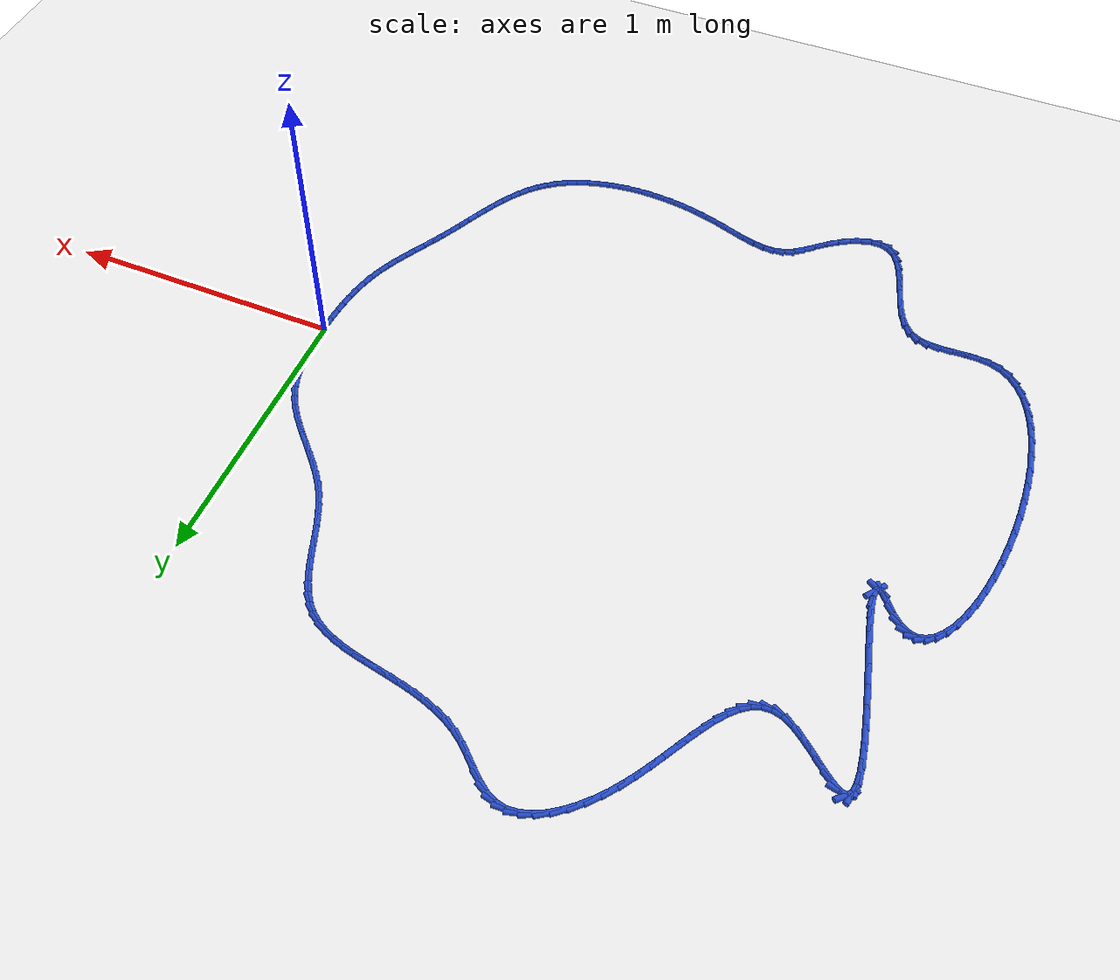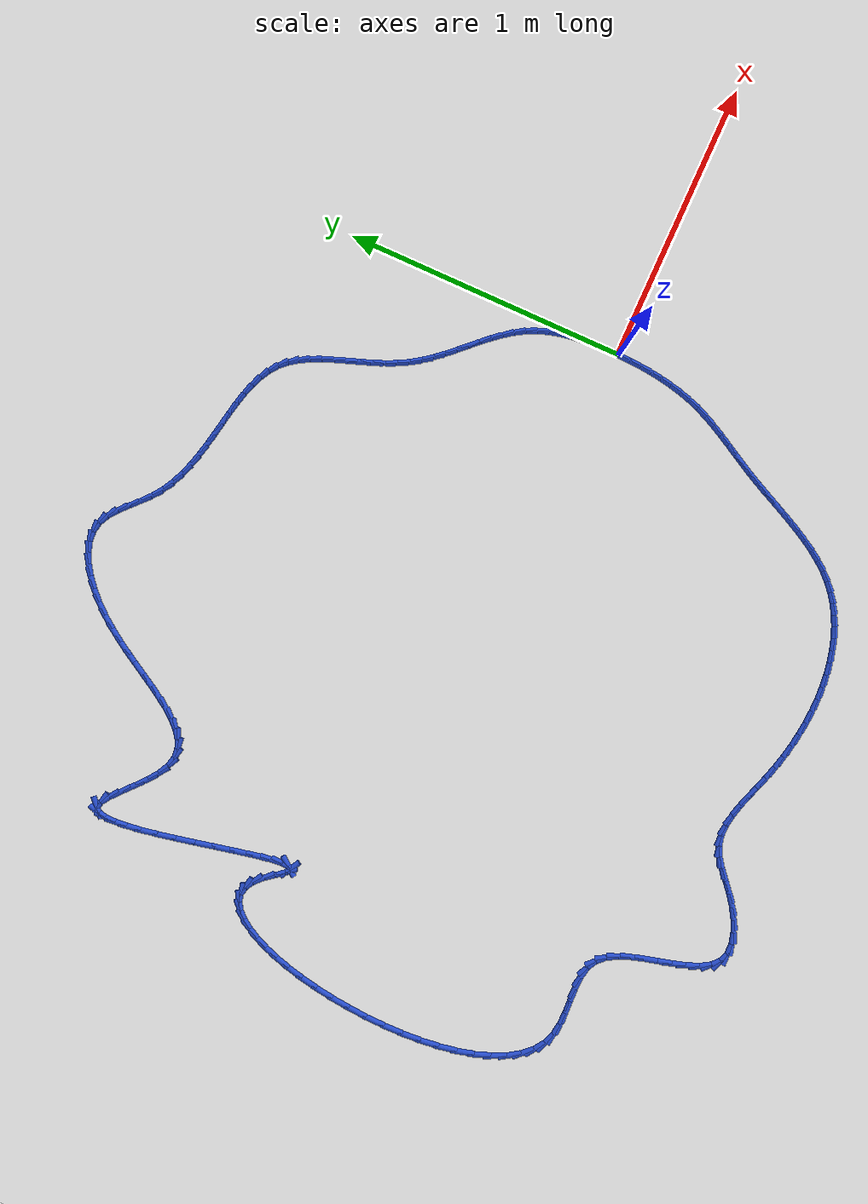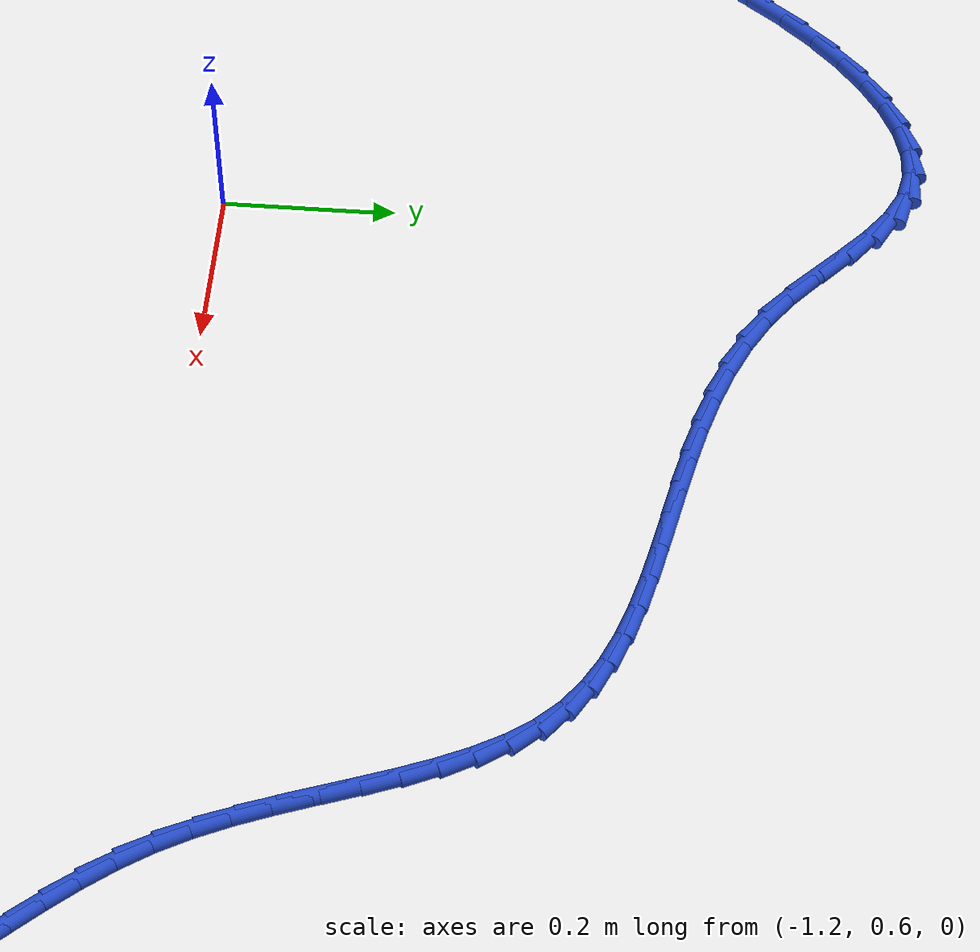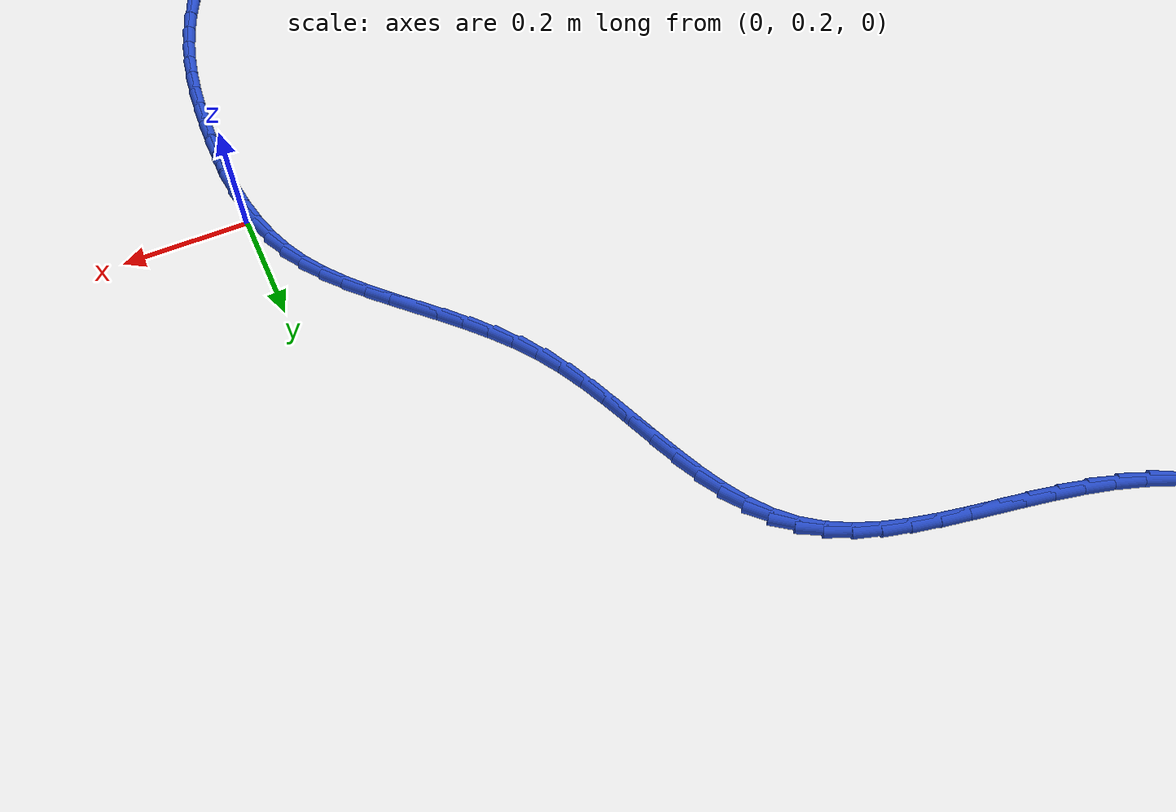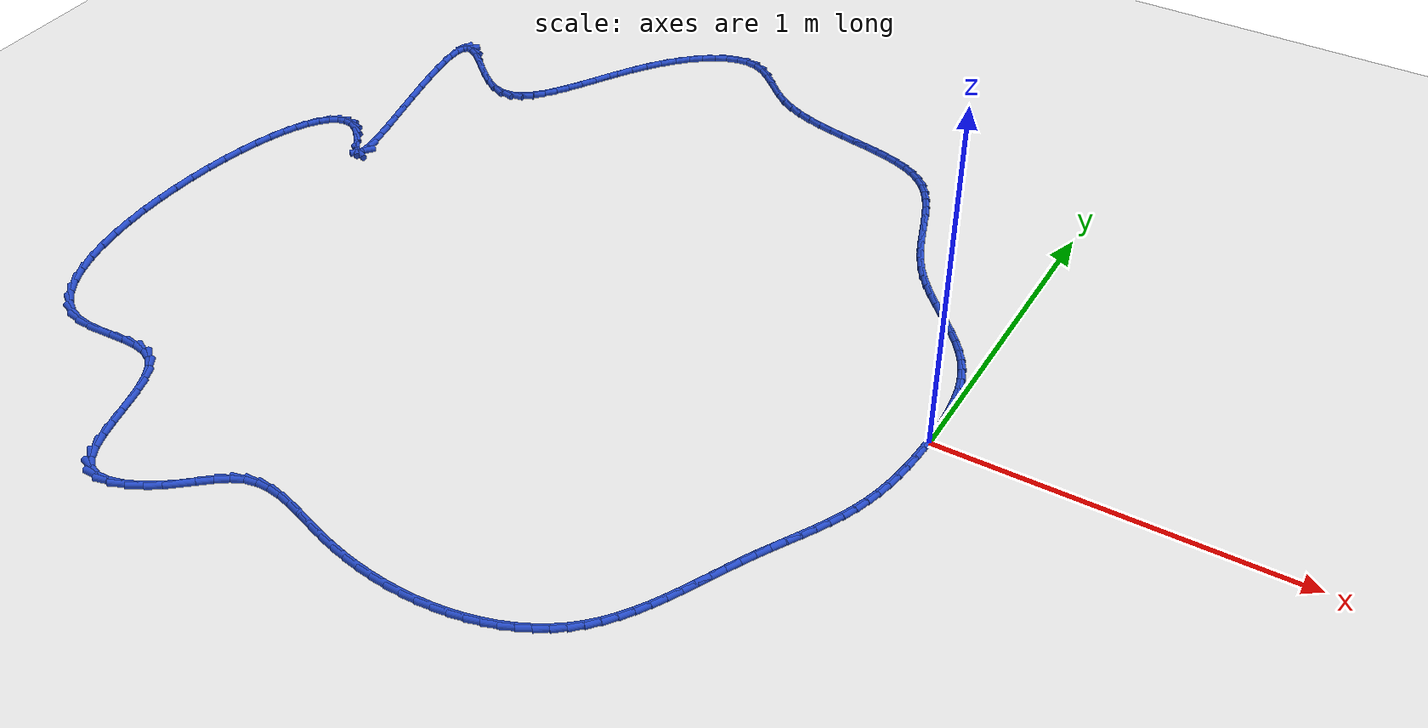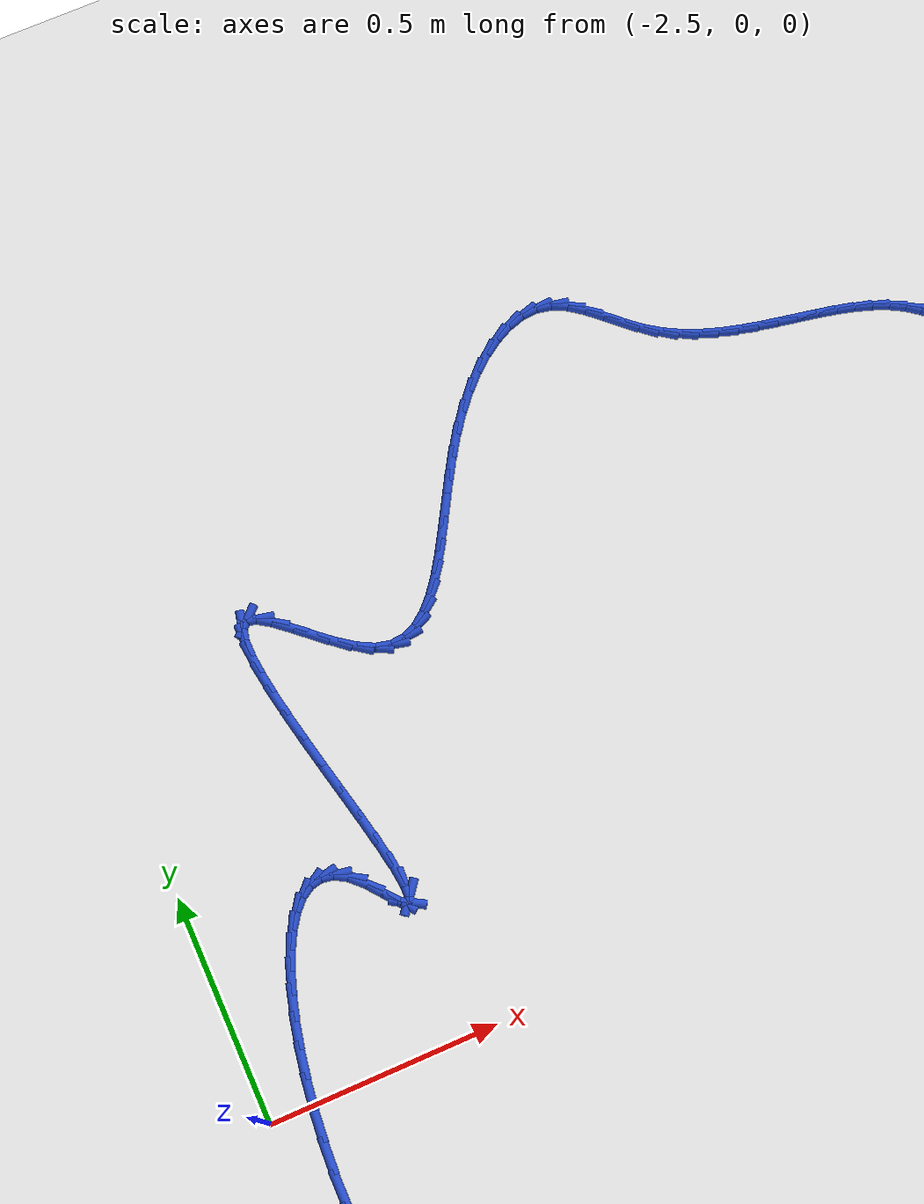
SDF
<sdf version="1.6">
 <world name="default">
  <light name="sun" type="directional">
   <pose>0 0 10 0 -0 0</pose>
   <diffuse>0.8 0.8 0.8 1</diffuse>
   <specular>0.2 0.2 0.2 1</specular>
   <attenuation>
    <range>1000</range>
    <constant>0.9</constant>
    <linear>0.01</linear>
    <quadratic>0.001</quadratic>
   </attenuation>
   <direction>-0.5 0.1 -0.9</direction>
  </light>
  <model name="ground_plane">
   <static>1</static>
   <link name="link">
    <collision name="collision">
     <geometry><plane><normal>0 0 1</normal><size>100 100</size></plane></geometry>
     <surface><friction><ode><mu>100</mu><mu2>50</mu2></ode></friction></surface>
    </collision>
    <visual name="visual">
     <cast_shadows>0</cast_shadows>
     <geometry><plane><normal>0 0 1</normal><size>100 100</size></plane></geometry>
     <material>
      <script><uri>file://media/materials/scripts/gazebo.material</uri><name>Gazebo/WhiteGlow</name></script>
     </material>
    </visual>
   </link>
  </model>
  <gravity>0 0 -9.8</gravity>
  <magnetic_field>6e-06 2.3e-05 -4.2e-05</magnetic_field>
  <atmosphere type="adiabatic"/>
  <physics name="default_physics" default="0" type="ode">
   <max_step_size>0.001</max_step_size>
   <real_time_factor>1</real_time_factor>
   <real_time_update_rate>1000</real_time_update_rate>
  </physics>
  <scene><ambient>0.4 0.4 0.4 1</ambient><background>0.7 0.7 0.7 1</background><shadows>1</shadows></scene>
  <spherical_coordinates>
   <surface_model>EARTH_WGS84</surface_model>
   <latitude_deg>0</latitude_deg>
   <longitude_deg>0</longitude_deg>
   <elevation>0</elevation>
   <heading_deg>0</heading_deg>
  </spherical_coordinates>
  <model name="line">
   <link name="link_0">
    <pose>-2.42861286636753e-17 2.0816681711721685e-17 0.01 0 1.57 1.5620864987343244</pose>
    <collision name="collision">
     <geometry><cylinder><radius>0.01</radius><length>0.08</length></cylinder></geometry>
    </collision>
    <visual name="visual">
     <material>
      <script><name>Gazebo/Blue</name><uri>file://media/materials/scripts/gazebo.material</uri></script>
     </material>
     <geometry><cylinder><radius>0.01</radius><length>0.08</length></cylinder></geometry>
    </visual>
   </link>
   <link name="link_1">
    <pose>0.00037207546715301747 0.042717956753290175 0.01 0 1.57 -1.547647721185586</pose>
    <collision name="collision">
     <geometry><cylinder><radius>0.01</radius><length>0.08</length></cylinder></geometry>
    </collision>
    <visual name="visual">
     <material>
      <script><name>Gazebo/Blue</name><uri>file://media/materials/scripts/gazebo.material</uri></script>
     </material>
     <geometry><cylinder><radius>0.01</radius><length>0.08</length></cylinder></geometry>
    </visual>
   </link>
   <link name="link_2">
    <pose>-0.000616630045460906 0.0854215615011634 0.01 0 1.57 -1.5065132838567732</pose>
    <collision name="collision">
     <geometry><cylinder><radius>0.01</radius><length>0.08</length></cylinder></geometry>
    </collision>
    <visual name="visual">
     <material>
      <script><name>Gazebo/Blue</name><uri>file://media/materials/scripts/gazebo.material</uri></script>
     </material>
     <geometry><cylinder><radius>0.01</radius><length>0.08</length></cylinder></geometry>
    </visual>
   </link>
   <link name="link_3">
    <pose>-0.0033436973060621744 0.12778591979551154 0.01 0 1.57 -1.4551755909871809</pose>
    <collision name="collision">
     <geometry><cylinder><radius>0.01</radius><length>0.08</length></cylinder></geometry>
    </collision>
    <visual name="visual">
     <material>
      <script><name>Gazebo/Blue</name><uri>file://media/materials/scripts/gazebo.material</uri></script>
     </material>
     <geometry><cylinder><radius>0.01</radius><length>0.08</length></cylinder></geometry>
    </visual>
   </link>
   <link name="link_4">
    <pose>-0.008186707082871177 0.16948613718822653 0.01 0 1.57 -1.392500677713814</pose>
    <collision name="collision">
     <geometry><cylinder><radius>0.01</radius><length>0.08</length></cylinder></geometry>
    </collision>
    <visual name="visual">
     <material>
      <script><name>Gazebo/Blue</name><uri>file://media/materials/scripts/gazebo.material</uri></script>
     </material>
     <geometry><cylinder><radius>0.01</radius><length>0.08</length></cylinder></geometry>
    </visual>
   </link>
   <link name="link_5">
    <pose>-0.015523240144108285 0.2101973192312003 0.01 0 1.57 -1.3172760069311842</pose>
    <collision name="collision">
     <geometry><cylinder><radius>0.01</radius><length>0.08</length></cylinder></geometry>
    </collision>
    <visual name="visual">
     <material>
      <script><name>Gazebo/Blue</name><uri>file://media/materials/scripts/gazebo.material</uri></script>
     </material>
     <geometry><cylinder><radius>0.01</radius><length>0.08</length></cylinder></geometry>
    </visual>
   </link>
   <link name="link_6">
    <pose>-0.025730877257993875 0.24959457147632452 0.01 0 1.57 -1.2284497367976805</pose>
    <collision name="collision">
     <geometry><cylinder><radius>0.01</radius><length>0.08</length></cylinder></geometry>
    </collision>
    <visual name="visual">
     <material>
      <script><name>Gazebo/Blue</name><uri>file://media/materials/scripts/gazebo.material</uri></script>
     </material>
     <geometry><cylinder><radius>0.01</radius><length>0.08</length></cylinder></geometry>
    </visual>
   </link>
   <link name="link_7">
    <pose>-0.03918719919274836 0.2873529994754913 0.01 0 1.57 -1.1258658671360646</pose>
    <collision name="collision">
     <geometry><cylinder><radius>0.01</radius><length>0.08</length></cylinder></geometry>
    </collision>
    <visual name="visual">
     <material>
      <script><name>Gazebo/Blue</name><uri>file://media/materials/scripts/gazebo.material</uri></script>
     </material>
     <geometry><cylinder><radius>0.01</radius><length>0.08</length></cylinder></geometry>
    </visual>
   </link>
   <link name="link_8">
    <pose>-0.05625864762224866 0.32315587455591566 0.01 0 1.57 -1.0234908410081385</pose>
    <collision name="collision">
     <geometry><cylinder><radius>0.01</radius><length>0.08</length></cylinder></geometry>
    </collision>
    <visual name="visual">
     <material>
      <script><name>Gazebo/Blue</name><uri>file://media/materials/scripts/gazebo.material</uri></script>
     </material>
     <geometry><cylinder><radius>0.01</radius><length>0.08</length></cylinder></geometry>
    </visual>
   </link>
   <link name="link_9">
    <pose>-0.07688356958069109 0.3570002928978009 0.01 0 1.57 -0.9403648433385308</pose>
    <collision name="collision">
     <geometry><cylinder><radius>0.01</radius><length>0.08</length></cylinder></geometry>
    </collision>
    <visual name="visual">
     <material>
      <script><name>Gazebo/Blue</name><uri>file://media/materials/scripts/gazebo.material</uri></script>
     </material>
     <geometry><cylinder><radius>0.01</radius><length>0.08</length></cylinder></geometry>
    </visual>
   </link>
   <link name="link_10">
    <pose>-0.10044704179031617 0.38928893850754065 0.01 0 1.57 -0.8783027276906727</pose>
    <collision name="collision">
     <geometry><cylinder><radius>0.01</radius><length>0.08</length></cylinder></geometry>
    </collision>
    <visual name="visual">
     <material>
      <script><name>Gazebo/Blue</name><uri>file://media/materials/scripts/gazebo.material</uri></script>
     </material>
     <geometry><cylinder><radius>0.01</radius><length>0.08</length></cylinder></geometry>
    </visual>
   </link>
   <link name="link_11">
    <pose>-0.12629744926571834 0.4204513931115435 0.01 0 1.57 -0.8367771793753681</pose>
    <collision name="collision">
     <geometry><cylinder><radius>0.01</radius><length>0.08</length></cylinder></geometry>
    </collision>
    <visual name="visual">
     <material>
      <script><name>Gazebo/Blue</name><uri>file://media/materials/scripts/gazebo.material</uri></script>
     </material>
     <geometry><cylinder><radius>0.01</radius><length>0.08</length></cylinder></geometry>
    </visual>
   </link>
   <link name="link_12">
    <pose>-0.1537831770214921 0.45091723843621834 0.01 0 1.57 -0.8148669827680531</pose>
    <collision name="collision">
     <geometry><cylinder><radius>0.01</radius><length>0.08</length></cylinder></geometry>
    </collision>
    <visual name="visual">
     <material>
      <script><name>Gazebo/Blue</name><uri>file://media/materials/scripts/gazebo.material</uri></script>
     </material>
     <geometry><cylinder><radius>0.01</radius><length>0.08</length></cylinder></geometry>
    </visual>
   </link>
   <link name="link_13">
    <pose>-0.18225261007223195 0.48111605620797343 0.01 0 1.57 -0.8117573754514157</pose>
    <collision name="collision">
     <geometry><cylinder><radius>0.01</radius><length>0.08</length></cylinder></geometry>
    </collision>
    <visual name="visual">
     <material>
      <script><name>Gazebo/Blue</name><uri>file://media/materials/scripts/gazebo.material</uri></script>
     </material>
     <geometry><cylinder><radius>0.01</radius><length>0.08</length></cylinder></geometry>
    </visual>
   </link>
   <link name="link_14">
    <pose>-0.2110541334325323 0.5114774281532175 0.01 0 1.57 -0.8269572624084032</pose>
    <collision name="collision">
     <geometry><cylinder><radius>0.01</radius><length>0.08</length></cylinder></geometry>
    </collision>
    <visual name="visual">
     <material>
      <script><name>Gazebo/Blue</name><uri>file://media/materials/scripts/gazebo.material</uri></script>
     </material>
     <geometry><cylinder><radius>0.01</radius><length>0.08</length></cylinder></geometry>
    </visual>
   </link>
   <link name="link_15">
    <pose>-0.2395361321169877 0.5424309359983592 0.01 0 1.57 -0.8603066581623194</pose>
    <collision name="collision">
     <geometry><cylinder><radius>0.01</radius><length>0.08</length></cylinder></geometry>
    </collision>
    <visual name="visual">
     <material>
      <script><name>Gazebo/Blue</name><uri>file://media/materials/scripts/gazebo.material</uri></script>
     </material>
     <geometry><cylinder><radius>0.01</radius><length>0.08</length></cylinder></geometry>
    </visual>
   </link>
   <link name="link_16">
    <pose>-0.2670469911401927 0.574406161469807 0.01 0 1.57 -0.9118125329983564</pose>
    <collision name="collision">
     <geometry><cylinder><radius>0.01</radius><length>0.08</length></cylinder></geometry>
    </collision>
    <visual name="visual">
     <material>
      <script><name>Gazebo/Blue</name><uri>file://media/materials/scripts/gazebo.material</uri></script>
     </material>
     <geometry><cylinder><radius>0.01</radius><length>0.08</length></cylinder></geometry>
    </visual>
   </link>
   <link name="link_17">
    <pose>-0.2929350955167416 0.6078326862939695 0.01 0 1.57 -0.9813154814949131</pose>
    <collision name="collision">
     <geometry><cylinder><radius>0.01</radius><length>0.08</length></cylinder></geometry>
    </collision>
    <visual name="visual">
     <material>
      <script><name>Gazebo/Blue</name><uri>file://media/materials/scripts/gazebo.material</uri></script>
     </material>
     <geometry><cylinder><radius>0.01</radius><length>0.08</length></cylinder></geometry>
    </visual>
   </link>
   <link name="link_18">
    <pose>-0.3165488302612288 0.6431400921972549 0.01 0 1.57 -1.0648535036615285</pose>
    <collision name="collision">
     <geometry><cylinder><radius>0.01</radius><length>0.08</length></cylinder></geometry>
    </collision>
    <visual name="visual">
     <material>
      <script><name>Gazebo/Blue</name><uri>file://media/materials/scripts/gazebo.material</uri></script>
     </material>
     <geometry><cylinder><radius>0.01</radius><length>0.08</length></cylinder></geometry>
    </visual>
   </link>
   <link name="link_19">
    <pose>-0.33734193857479833 0.6806697876710137 0.01 0 1.57 -1.1371374138150026</pose>
    <collision name="collision">
     <geometry><cylinder><radius>0.01</radius><length>0.08</length></cylinder></geometry>
    </collision>
    <visual name="visual">
     <material>
      <script><name>Gazebo/Blue</name><uri>file://media/materials/scripts/gazebo.material</uri></script>
     </material>
     <geometry><cylinder><radius>0.01</radius><length>0.08</length></cylinder></geometry>
    </visual>
   </link>
   <link name="link_20">
    <pose>-0.35558926507172944 0.7200760094710266 0.01 0 1.57 -1.1878325797074916</pose>
    <collision name="collision">
     <geometry><cylinder><radius>0.01</radius><length>0.08</length></cylinder></geometry>
    </collision>
    <visual name="visual">
     <material>
      <script><name>Gazebo/Blue</name><uri>file://media/materials/scripts/gazebo.material</uri></script>
     </material>
     <geometry><cylinder><radius>0.01</radius><length>0.08</length></cylinder></geometry>
    </visual>
   </link>
   <link name="link_21">
    <pose>-0.37195096259407945 0.760690533668711 0.01 0 1.57 -1.2183001767137382</pose>
    <collision name="collision">
     <geometry><cylinder><radius>0.01</radius><length>0.08</length></cylinder></geometry>
    </collision>
    <visual name="visual">
     <material>
      <script><name>Gazebo/Blue</name><uri>file://media/materials/scripts/gazebo.material</uri></script>
     </material>
     <geometry><cylinder><radius>0.01</radius><length>0.08</length></cylinder></geometry>
    </visual>
   </link>
   <link name="link_22">
    <pose>-0.3870894042844929 0.8018432781876569 0.01 0 1.57 -1.2293462711053924</pose>
    <collision name="collision">
     <geometry><cylinder><radius>0.01</radius><length>0.08</length></cylinder></geometry>
    </collision>
    <visual name="visual">
     <material>
      <script><name>Gazebo/Blue</name><uri>file://media/materials/scripts/gazebo.material</uri></script>
     </material>
     <geometry><cylinder><radius>0.01</radius><length>0.08</length></cylinder></geometry>
    </visual>
   </link>
   <link name="link_23">
    <pose>-0.4016669632856135 0.8428641609514534 0.01 0 1.57 -1.2208404121530485</pose>
    <collision name="collision">
     <geometry><cylinder><radius>0.01</radius><length>0.08</length></cylinder></geometry>
    </collision>
    <visual name="visual">
     <material>
      <script><name>Gazebo/Blue</name><uri>file://media/materials/scripts/gazebo.material</uri></script>
     </material>
     <geometry><cylinder><radius>0.01</radius><length>0.08</length></cylinder></geometry>
    </visual>
   </link>
   <link name="link_24">
    <pose>-0.4163460127400854 0.88308309988369 0.01 0 1.57 -1.1915332056967973</pose>
    <collision name="collision">
     <geometry><cylinder><radius>0.01</radius><length>0.08</length></cylinder></geometry>
    </collision>
    <visual name="visual">
     <material>
      <script><name>Gazebo/Blue</name><uri>file://media/materials/scripts/gazebo.material</uri></script>
     </material>
     <geometry><cylinder><radius>0.01</radius><length>0.08</length></cylinder></geometry>
    </visual>
   </link>
   <link name="link_25">
    <pose>-0.4317889257905527 0.9218300129079567 0.01 0 1.57 -1.1389601954534163</pose>
    <collision name="collision">
     <geometry><cylinder><radius>0.01</radius><length>0.08</length></cylinder></geometry>
    </collision>
    <visual name="visual">
     <material>
      <script><name>Gazebo/Blue</name><uri>file://media/materials/scripts/gazebo.material</uri></script>
     </material>
     <geometry><cylinder><radius>0.01</radius><length>0.08</length></cylinder></geometry>
    </visual>
   </link>
   <link name="link_26">
    <pose>-0.44865807557965953 0.9584348179478428 0.01 0 1.57 -1.0595447518045487</pose>
    <collision name="collision">
     <geometry><cylinder><radius>0.01</radius><length>0.08</length></cylinder></geometry>
    </collision>
    <visual name="visual">
     <material>
      <script><name>Gazebo/Blue</name><uri>file://media/materials/scripts/gazebo.material</uri></script>
     </material>
     <geometry><cylinder><radius>0.01</radius><length>0.08</length></cylinder></geometry>
    </visual>
   </link>
   <link name="link_27">
    <pose>-0.4676158352500499 0.9922274329269377 0.01 0 1.57 -0.9492700592249191</pose>
    <collision name="collision">
     <geometry><cylinder><radius>0.01</radius><length>0.08</length></cylinder></geometry>
    </collision>
    <visual name="visual">
     <material>
      <script><name>Gazebo/Blue</name><uri>file://media/materials/scripts/gazebo.material</uri></script>
     </material>
     <geometry><cylinder><radius>0.01</radius><length>0.08</length></cylinder></geometry>
    </visual>
   </link>
   <link name="link_28">
    <pose>-0.4893245779443679 1.0225377757688312 0.01 0 1.57 -0.8057340985343729</pose>
    <collision name="collision">
     <geometry><cylinder><radius>0.01</radius><length>0.08</length></cylinder></geometry>
    </collision>
    <visual name="visual">
     <material>
      <script><name>Gazebo/Blue</name><uri>file://media/materials/scripts/gazebo.material</uri></script>
     </material>
     <geometry><cylinder><radius>0.01</radius><length>0.08</length></cylinder></geometry>
    </visual>
   </link>
   <link name="link_29">
    <pose>-0.5144434227529491 1.048699604814113 0.01 0 1.57 -0.6466422261593727</pose>
    <collision name="collision">
     <geometry><cylinder><radius>0.01</radius><length>0.08</length></cylinder></geometry>
    </collision>
    <visual name="visual">
     <material>
      <script><name>Gazebo/Blue</name><uri>file://media/materials/scripts/gazebo.material</uri></script>
     </material>
     <geometry><cylinder><radius>0.01</radius><length>0.08</length></cylinder></geometry>
    </visual>
   </link>
   <link name="link_30">
    <pose>-0.5432761767328922 1.0704660159688784 0.01 0 1.57 -0.5079842084404306</pose>
    <collision name="collision">
     <geometry><cylinder><radius>0.01</radius><length>0.08</length></cylinder></geometry>
    </collision>
    <visual name="visual">
     <material>
      <script><name>Gazebo/Blue</name><uri>file://media/materials/scripts/gazebo.material</uri></script>
     </material>
     <geometry><cylinder><radius>0.01</radius><length>0.08</length></cylinder></geometry>
    </visual>
   </link>
   <link name="link_31">
    <pose>-0.5754563378831818 1.088381200689813 0.01 0 1.57 -0.3966448983229426</pose>
    <collision name="collision">
     <geometry><cylinder><radius>0.01</radius><length>0.08</length></cylinder></geometry>
    </collision>
    <visual name="visual">
     <material>
      <script><name>Gazebo/Blue</name><uri>file://media/materials/scripts/gazebo.material</uri></script>
     </material>
     <geometry><cylinder><radius>0.01</radius><length>0.08</length></cylinder></geometry>
    </visual>
   </link>
   <link name="link_32">
    <pose>-0.6105430778655511 1.10307707002202 0.01 0 1.57 -0.3119156909555713</pose>
    <collision name="collision">
     <geometry><cylinder><radius>0.01</radius><length>0.08</length></cylinder></geometry>
    </collision>
    <visual name="visual">
     <material>
      <script><name>Gazebo/Blue</name><uri>file://media/materials/scripts/gazebo.material</uri></script>
     </material>
     <geometry><cylinder><radius>0.01</radius><length>0.08</length></cylinder></geometry>
    </visual>
   </link>
   <link name="link_33">
    <pose>-0.6480955683417341 1.1151855350106041 0.01 0 1.57 -0.25111926044509847</pose>
    <collision name="collision">
     <geometry><cylinder><radius>0.01</radius><length>0.08</length></cylinder></geometry>
    </collision>
    <visual name="visual">
     <material>
      <script><name>Gazebo/Blue</name><uri>file://media/materials/scripts/gazebo.material</uri></script>
     </material>
     <geometry><cylinder><radius>0.01</radius><length>0.08</length></cylinder></geometry>
    </visual>
   </link>
   <link name="link_34">
    <pose>-0.6876729809734647 1.1253385067006678 0.01 0 1.57 -0.21130392288726207</pose>
    <collision name="collision">
     <geometry><cylinder><radius>0.01</radius><length>0.08</length></cylinder></geometry>
    </collision>
    <visual name="visual">
     <material>
      <script><name>Gazebo/Blue</name><uri>file://media/materials/scripts/gazebo.material</uri></script>
     </material>
     <geometry><cylinder><radius>0.01</radius><length>0.08</length></cylinder></geometry>
    </visual>
   </link>
   <link name="link_35">
    <pose>-0.7288344874224764 1.1341678961373154 0.01 0 1.57 -0.19003809825175072</pose>
    <collision name="collision">
     <geometry><cylinder><radius>0.01</radius><length>0.08</length></cylinder></geometry>
    </collision>
    <visual name="visual">
     <material>
      <script><name>Gazebo/Blue</name><uri>file://media/materials/scripts/gazebo.material</uri></script>
     </material>
     <geometry><cylinder><radius>0.01</radius><length>0.08</length></cylinder></geometry>
    </visual>
   </link>
   <link name="link_36">
    <pose>-0.7711392593505028 1.14230561436565 0.01 0 1.57 -0.18566479154197033</pose>
    <collision name="collision">
     <geometry><cylinder><radius>0.01</radius><length>0.08</length></cylinder></geometry>
    </collision>
    <visual name="visual">
     <material>
      <script><name>Gazebo/Blue</name><uri>file://media/materials/scripts/gazebo.material</uri></script>
     </material>
     <geometry><cylinder><radius>0.01</radius><length>0.08</length></cylinder></geometry>
    </visual>
   </link>
   <link name="link_37">
    <pose>-0.8141464684192783 1.1503835724307756 0.01 0 1.57 -0.19731434381740204</pose>
    <collision name="collision">
     <geometry><cylinder><radius>0.01</radius><length>0.08</length></cylinder></geometry>
    </collision>
    <visual name="visual">
     <material>
      <script><name>Gazebo/Blue</name><uri>file://media/materials/scripts/gazebo.material</uri></script>
     </material>
     <geometry><cylinder><radius>0.01</radius><length>0.08</length></cylinder></geometry>
    </visual>
   </link>
   <link name="link_38">
    <pose>-0.857415286290536 1.1590336813777957 0.01 0 1.57 -0.22482408421275132</pose>
    <collision name="collision">
     <geometry><cylinder><radius>0.01</radius><length>0.08</length></cylinder></geometry>
    </collision>
    <visual name="visual">
     <material>
      <script><name>Gazebo/Blue</name><uri>file://media/materials/scripts/gazebo.material</uri></script>
     </material>
     <geometry><cylinder><radius>0.01</radius><length>0.08</length></cylinder></geometry>
    </visual>
   </link>
   <link name="link_39">
    <pose>-0.9005048846260102 1.1688878522518136 0.01 0 1.57 -0.26860737601872353</pose>
    <collision name="collision">
     <geometry><cylinder><radius>0.01</radius><length>0.08</length></cylinder></geometry>
    </collision>
    <visual name="visual">
     <material>
      <script><name>Gazebo/Blue</name><uri>file://media/materials/scripts/gazebo.material</uri></script>
     </material>
     <geometry><cylinder><radius>0.01</radius><length>0.08</length></cylinder></geometry>
    </visual>
   </link>
   <link name="link_40">
    <pose>-0.9429744350874343 1.1805779960979335 0.01 0 1.57 -0.329449333892676</pose>
    <collision name="collision">
     <geometry><cylinder><radius>0.01</radius><length>0.08</length></cylinder></geometry>
    </collision>
    <visual name="visual">
     <material>
      <script><name>Gazebo/Blue</name><uri>file://media/materials/scripts/gazebo.material</uri></script>
     </material>
     <geometry><cylinder><radius>0.01</radius><length>0.08</length></cylinder></geometry>
    </visual>
   </link>
   <link name="link_41">
    <pose>-0.9843831093365423 1.1947360239612588 0.01 0 1.57 -0.40816504107593854</pose>
    <collision name="collision">
     <geometry><cylinder><radius>0.01</radius><length>0.08</length></cylinder></geometry>
    </collision>
    <visual name="visual">
     <material>
      <script><name>Gazebo/Blue</name><uri>file://media/materials/scripts/gazebo.material</uri></script>
     </material>
     <geometry><cylinder><radius>0.01</radius><length>0.08</length></cylinder></geometry>
    </visual>
   </link>
   <link name="link_42">
    <pose>-1.0242900790350677 1.2119938468868927 0.01 0 1.57 -0.5050466349754343</pose>
    <collision name="collision">
     <geometry><cylinder><radius>0.01</radius><length>0.08</length></cylinder></geometry>
    </collision>
    <visual name="visual">
     <material>
      <script><name>Gazebo/Blue</name><uri>file://media/materials/scripts/gazebo.material</uri></script>
     </material>
     <geometry><cylinder><radius>0.01</radius><length>0.08</length></cylinder></geometry>
    </visual>
   </link>
   <link name="link_43">
    <pose>-1.0622545158447445 1.2329833759199391 0.01 0 1.57 -0.618666435638847</pose>
    <collision name="collision">
     <geometry><cylinder><radius>0.01</radius><length>0.08</length></cylinder></geometry>
    </collision>
    <visual name="visual">
     <material>
      <script><name>Gazebo/Blue</name><uri>file://media/materials/scripts/gazebo.material</uri></script>
     </material>
     <geometry><cylinder><radius>0.01</radius><length>0.08</length></cylinder></geometry>
    </visual>
   </link>
   <link name="link_44">
    <pose>-1.0978425393630487 1.258318407421768 0.01 0 1.57 -0.7179241758423572</pose>
    <collision name="collision">
     <geometry><cylinder><radius>0.01</radius><length>0.08</length></cylinder></geometry>
    </collision>
    <visual name="visual">
     <material>
      <script><name>Gazebo/Blue</name><uri>file://media/materials/scripts/gazebo.material</uri></script>
     </material>
     <geometry><cylinder><radius>0.01</radius><length>0.08</length></cylinder></geometry>
    </visual>
   </link>
   <link name="link_45">
    <pose>-1.131098978446382 1.287364645205541 0.01 0 1.57 -0.7585628702160012</pose>
    <collision name="collision">
     <geometry><cylinder><radius>0.01</radius><length>0.08</length></cylinder></geometry>
    </collision>
    <visual name="visual">
     <material>
      <script><name>Gazebo/Blue</name><uri>file://media/materials/scripts/gazebo.material</uri></script>
     </material>
     <geometry><cylinder><radius>0.01</radius><length>0.08</length></cylinder></geometry>
    </visual>
   </link>
   <link name="link_46">
    <pose>-1.1628485845207308 1.3174543760799788 0.01 0 1.57 -0.7372889719506099</pose>
    <collision name="collision">
     <geometry><cylinder><radius>0.01</radius><length>0.08</length></cylinder></geometry>
    </collision>
    <visual name="visual">
     <material>
      <script><name>Gazebo/Blue</name><uri>file://media/materials/scripts/gazebo.material</uri></script>
     </material>
     <geometry><cylinder><radius>0.01</radius><length>0.08</length></cylinder></geometry>
    </visual>
   </link>
   <link name="link_47">
    <pose>-1.1939878359994052 1.3457328799874964 0.01 0 1.57 -0.6443869454229623</pose>
    <collision name="collision">
     <geometry><cylinder><radius>0.01</radius><length>0.08</length></cylinder></geometry>
    </collision>
    <visual name="visual">
     <material>
      <script><name>Gazebo/Blue</name><uri>file://media/materials/scripts/gazebo.material</uri></script>
     </material>
     <geometry><cylinder><radius>0.01</radius><length>0.08</length></cylinder></geometry>
    </visual>
   </link>
   <link name="link_48">
    <pose>-1.2254132112957157 1.3693454368705085 0.01 0 1.57 -0.4584365714877746</pose>
    <collision name="collision">
     <geometry><cylinder><radius>0.01</radius><length>0.08</length></cylinder></geometry>
    </collision>
    <visual name="visual">
     <material>
      <script><name>Gazebo/Blue</name><uri>file://media/materials/scripts/gazebo.material</uri></script>
     </material>
     <geometry><cylinder><radius>0.01</radius><length>0.08</length></cylinder></geometry>
    </visual>
   </link>
   <link name="link_49">
    <pose>-1.2580211097395646 1.3854375349294932 0.01 0 1.57 -0.18600717469215686</pose>
    <collision name="collision">
     <geometry><cylinder><radius>0.01</radius><length>0.08</length></cylinder></geometry>
    </collision>
    <visual name="visual">
     <material>
      <script><name>Gazebo/Blue</name><uri>file://media/materials/scripts/gazebo.material</uri></script>
     </material>
     <geometry><cylinder><radius>0.01</radius><length>0.08</length></cylinder></geometry>
    </visual>
   </link>
   <link name="link_50">
    <pose>-1.2924207423937293 1.3919109432861934 0.01 0 1.57 0.07751048192360882</pose>
    <collision name="collision">
     <geometry><cylinder><radius>0.01</radius><length>0.08</length></cylinder></geometry>
    </collision>
    <visual name="visual">
     <material>
      <script><name>Gazebo/Blue</name><uri>file://media/materials/scripts/gazebo.material</uri></script>
     </material>
     <geometry><cylinder><radius>0.01</radius><length>0.08</length></cylinder></geometry>
    </visual>
   </link>
   <link name="link_51">
    <pose>-1.3282879846106181 1.3891252751725964 0.01 0 1.57 0.29494766049136717</pose>
    <collision name="collision">
     <geometry><cylinder><radius>0.01</radius><length>0.08</length></cylinder></geometry>
    </collision>
    <visual name="visual">
     <material>
      <script><name>Gazebo/Blue</name><uri>file://media/materials/scripts/gazebo.material</uri></script>
     </material>
     <geometry><cylinder><radius>0.01</radius><length>0.08</length></cylinder></geometry>
    </visual>
   </link>
   <link name="link_52">
    <pose>-1.365109434739487 1.3779385854448991 0.01 0 1.57 0.4657607186810607</pose>
    <collision name="collision">
     <geometry><cylinder><radius>0.01</radius><length>0.08</length></cylinder></geometry>
    </collision>
    <visual name="visual">
     <material>
      <script><name>Gazebo/Blue</name><uri>file://media/materials/scripts/gazebo.material</uri></script>
     </material>
     <geometry><cylinder><radius>0.01</radius><length>0.08</length></cylinder></geometry>
    </visual>
   </link>
   <link name="link_53">
    <pose>-1.4023716911295903 1.359208928959297 0.01 0 1.57 0.5994824240193372</pose>
    <collision name="collision">
     <geometry><cylinder><radius>0.01</radius><length>0.08</length></cylinder></geometry>
    </collision>
    <visual name="visual">
     <material>
      <script><name>Gazebo/Blue</name><uri>file://media/materials/scripts/gazebo.material</uri></script>
     </material>
     <geometry><cylinder><radius>0.01</radius><length>0.08</length></cylinder></geometry>
    </visual>
   </link>
   <link name="link_54">
    <pose>-1.439561352130183 1.3337943605719869 0.01 0 1.57 0.7065256217840215</pose>
    <collision name="collision">
     <geometry><cylinder><radius>0.01</radius><length>0.08</length></cylinder></geometry>
    </collision>
    <visual name="visual">
     <material>
      <script><name>Gazebo/Blue</name><uri>file://media/materials/scripts/gazebo.material</uri></script>
     </material>
     <geometry><cylinder><radius>0.01</radius><length>0.08</length></cylinder></geometry>
    </visual>
   </link>
   <link name="link_55">
    <pose>-1.4761650160905198 1.302552935139165 0.01 0 1.57 0.7952419135481348</pose>
    <collision name="collision">
     <geometry><cylinder><radius>0.01</radius><length>0.08</length></cylinder></geometry>
    </collision>
    <visual name="visual">
     <material>
      <script><name>Gazebo/Blue</name><uri>file://media/materials/scripts/gazebo.material</uri></script>
     </material>
     <geometry><cylinder><radius>0.01</radius><length>0.08</length></cylinder></geometry>
    </visual>
   </link>
   <link name="link_56">
    <pose>-1.511669281359856 1.2663427075170277 0.01 0 1.57 0.8718189264634538</pose>
    <collision name="collision">
     <geometry><cylinder><radius>0.01</radius><length>0.08</length></cylinder></geometry>
    </collision>
    <visual name="visual">
     <material>
      <script><name>Gazebo/Blue</name><uri>file://media/materials/scripts/gazebo.material</uri></script>
     </material>
     <geometry><cylinder><radius>0.01</radius><length>0.08</length></cylinder></geometry>
    </visual>
   </link>
   <link name="link_57">
    <pose>-1.545560746287446 1.2260217325617713 0.01 0 1.57 0.9396032420666363</pose>
    <collision name="collision">
     <geometry><cylinder><radius>0.01</radius><length>0.08</length></cylinder></geometry>
    </collision>
    <visual name="visual">
     <material>
      <script><name>Gazebo/Blue</name><uri>file://media/materials/scripts/gazebo.material</uri></script>
     </material>
     <geometry><cylinder><radius>0.01</radius><length>0.08</length></cylinder></geometry>
    </visual>
   </link>
   <link name="link_58">
    <pose>-1.5773936114483118 1.1824713648348737 0.01 0 1.57 0.9917300465042784</pose>
    <collision name="collision">
     <geometry><cylinder><radius>0.01</radius><length>0.08</length></cylinder></geometry>
    </collision>
    <visual name="visual">
     <material>
      <script><name>Gazebo/Blue</name><uri>file://media/materials/scripts/gazebo.material</uri></script>
     </material>
     <geometry><cylinder><radius>0.01</radius><length>0.08</length></cylinder></geometry>
    </visual>
   </link>
   <link name="link_59">
    <pose>-1.6072782506019456 1.1367646489070746 0.01 0 1.57 1.0256263440788171</pose>
    <collision name="collision">
     <geometry><cylinder><radius>0.01</radius><length>0.08</length></cylinder></geometry>
    </collision>
    <visual name="visual">
     <material>
      <script><name>Gazebo/Blue</name><uri>file://media/materials/scripts/gazebo.material</uri></script>
     </material>
     <geometry><cylinder><radius>0.01</radius><length>0.08</length></cylinder></geometry>
    </visual>
   </link>
   <link name="link_60">
    <pose>-1.6355983027410979 1.0900688126297133 0.01 0 1.57 1.0426250279899079</pose>
    <collision name="collision">
     <geometry><cylinder><radius>0.01</radius><length>0.08</length></cylinder></geometry>
    </collision>
    <visual name="visual">
     <material>
      <script><name>Gazebo/Blue</name><uri>file://media/materials/scripts/gazebo.material</uri></script>
     </material>
     <geometry><cylinder><radius>0.01</radius><length>0.08</length></cylinder></geometry>
    </visual>
   </link>
   <link name="link_61">
    <pose>-1.6627393020520749 1.0435517370493579 0.01 0 1.57 1.0427539080265786</pose>
    <collision name="collision">
     <geometry><cylinder><radius>0.01</radius><length>0.08</length></cylinder></geometry>
    </collision>
    <visual name="visual">
     <material>
      <script><name>Gazebo/Blue</name><uri>file://media/materials/scripts/gazebo.material</uri></script>
     </material>
     <geometry><cylinder><radius>0.01</radius><length>0.08</length></cylinder></geometry>
    </visual>
   </link>
   <link name="link_62">
    <pose>-1.689086782721183 0.9983813032125762 0.01 0 1.57 1.0244347475375162</pose>
    <collision name="collision">
     <geometry><cylinder><radius>0.01</radius><length>0.08</length></cylinder></geometry>
    </collision>
    <visual name="visual">
     <material>
      <script><name>Gazebo/Blue</name><uri>file://media/materials/scripts/gazebo.material</uri></script>
     </material>
     <geometry><cylinder><radius>0.01</radius><length>0.08</length></cylinder></geometry>
    </visual>
   </link>
   <link name="link_63">
    <pose>-1.7150262789347281 0.9557253921659353 0.01 0 1.57 0.983954441137945</pose>
    <collision name="collision">
     <geometry><cylinder><radius>0.01</radius><length>0.08</length></cylinder></geometry>
    </collision>
    <visual name="visual">
     <material>
      <script><name>Gazebo/Blue</name><uri>file://media/materials/scripts/gazebo.material</uri></script>
     </material>
     <geometry><cylinder><radius>0.01</radius><length>0.08</length></cylinder></geometry>
    </visual>
   </link>
   <link name="link_64">
    <pose>-1.740943324879016 0.9167518849560031 0.01 0 1.57 0.9145210529931135</pose>
    <collision name="collision">
     <geometry><cylinder><radius>0.01</radius><length>0.08</length></cylinder></geometry>
    </collision>
    <visual name="visual">
     <material>
      <script><name>Gazebo/Blue</name><uri>file://media/materials/scripts/gazebo.material</uri></script>
     </material>
     <geometry><cylinder><radius>0.01</radius><length>0.08</length></cylinder></geometry>
    </visual>
   </link>
   <link name="link_65">
    <pose>-1.7672234547403538 0.8826286626293472 0.01 0 1.57 0.8049174356338774</pose>
    <collision name="collision">
     <geometry><cylinder><radius>0.01</radius><length>0.08</length></cylinder></geometry>
    </collision>
    <visual name="visual">
     <material>
      <script><name>Gazebo/Blue</name><uri>file://media/materials/scripts/gazebo.material</uri></script>
     </material>
     <geometry><cylinder><radius>0.01</radius><length>0.08</length></cylinder></geometry>
    </visual>
   </link>
   <link name="link_66">
    <pose>-1.794252202705047 0.8545236062325354 0.01 0 1.57 0.6388681710043597</pose>
    <collision name="collision">
     <geometry><cylinder><radius>0.01</radius><length>0.08</length></cylinder></geometry>
    </collision>
    <visual name="visual">
     <material>
      <script><name>Gazebo/Blue</name><uri>file://media/materials/scripts/gazebo.material</uri></script>
     </material>
     <geometry><cylinder><radius>0.01</radius><length>0.08</length></cylinder></geometry>
    </visual>
   </link>
   <link name="link_67">
    <pose>-1.8224151029594011 0.833604596812135 0.01 0 1.57 0.40044249190699444</pose>
    <collision name="collision">
     <geometry><cylinder><radius>0.01</radius><length>0.08</length></cylinder></geometry>
    </collision>
    <visual name="visual">
     <material>
      <script><name>Gazebo/Blue</name><uri>file://media/materials/scripts/gazebo.material</uri></script>
     </material>
     <geometry><cylinder><radius>0.01</radius><length>0.08</length></cylinder></geometry>
    </visual>
   </link>
   <link name="link_68">
    <pose>-1.8520976896897237 0.8210395154147139 0.01 0 1.57 0.09604682197793155</pose>
    <collision name="collision">
     <geometry><cylinder><radius>0.01</radius><length>0.08</length></cylinder></geometry>
    </collision>
    <visual name="visual">
     <material>
      <script><name>Gazebo/Blue</name><uri>file://media/materials/scripts/gazebo.material</uri></script>
     </material>
     <geometry><cylinder><radius>0.01</radius><length>0.08</length></cylinder></geometry>
    </visual>
   </link>
   <link name="link_69">
    <pose>-1.88368549708232 0.8179962430868395 0.01 0 1.57 -0.22198135086465193</pose>
    <collision name="collision">
     <geometry><cylinder><radius>0.01</radius><length>0.08</length></cylinder></geometry>
    </collision>
    <visual name="visual">
     <material>
      <script><name>Gazebo/Blue</name><uri>file://media/materials/scripts/gazebo.material</uri></script>
     </material>
     <geometry><cylinder><radius>0.01</radius><length>0.08</length></cylinder></geometry>
    </visual>
   </link>
   <link name="link_70">
    <pose>-1.9175640593234964 0.8256426608750795 0.01 0 1.57 -0.4845064492717018</pose>
    <collision name="collision">
     <geometry><cylinder><radius>0.01</radius><length>0.08</length></cylinder></geometry>
    </collision>
    <visual name="visual">
     <material>
      <script><name>Gazebo/Blue</name><uri>file://media/materials/scripts/gazebo.material</uri></script>
     </material>
     <geometry><cylinder><radius>0.01</radius><length>0.08</length></cylinder></geometry>
    </visual>
   </link>
   <link name="link_71">
    <pose>-1.95400169011768 0.8448216883925188 0.01 0 1.57 -0.6372565025701054</pose>
    <collision name="collision">
     <geometry><cylinder><radius>0.01</radius><length>0.08</length></cylinder></geometry>
    </collision>
    <visual name="visual">
     <material>
      <script><name>Gazebo/Blue</name><uri>file://media/materials/scripts/gazebo.material</uri></script>
     </material>
     <geometry><cylinder><radius>0.01</radius><length>0.08</length></cylinder></geometry>
    </visual>
   </link>
   <link name="link_72">
    <pose>-1.9920426819742527 0.8729829843154018 0.01 0 1.57 -0.709179409702418</pose>
    <collision name="collision">
     <geometry><cylinder><radius>0.01</radius><length>0.08</length></cylinder></geometry>
    </collision>
    <visual name="visual">
     <material>
      <script><name>Gazebo/Blue</name><uri>file://media/materials/scripts/gazebo.material</uri></script>
     </material>
     <geometry><cylinder><radius>0.01</radius><length>0.08</length></cylinder></geometry>
    </visual>
   </link>
   <link name="link_73">
    <pose>-2.0300028538674373 0.9055567155004101 0.01 0 1.57 -0.7300996747330574</pose>
    <collision name="collision">
     <geometry><cylinder><radius>0.01</radius><length>0.08</length></cylinder></geometry>
    </collision>
    <visual name="visual">
     <material>
      <script><name>Gazebo/Blue</name><uri>file://media/materials/scripts/gazebo.material</uri></script>
     </material>
     <geometry><cylinder><radius>0.01</radius><length>0.08</length></cylinder></geometry>
    </visual>
   </link>
   <link name="link_74">
    <pose>-2.0661883596268003 0.9379462548582148 0.01 0 1.57 -0.7009214867870286</pose>
    <collision name="collision">
     <geometry><cylinder><radius>0.01</radius><length>0.08</length></cylinder></geometry>
    </collision>
    <visual name="visual">
     <material>
      <script><name>Gazebo/Blue</name><uri>file://media/materials/scripts/gazebo.material</uri></script>
     </material>
     <geometry><cylinder><radius>0.01</radius><length>0.08</length></cylinder></geometry>
    </visual>
   </link>
   <link name="link_75">
    <pose>-2.098905353081909 0.9655549752994868 0.01 0 1.57 -0.5845151752134596</pose>
    <collision name="collision">
     <geometry><cylinder><radius>0.01</radius><length>0.08</length></cylinder></geometry>
    </collision>
    <visual name="visual">
     <material>
      <script><name>Gazebo/Blue</name><uri>file://media/materials/scripts/gazebo.material</uri></script>
     </material>
     <geometry><cylinder><radius>0.01</radius><length>0.08</length></cylinder></geometry>
    </visual>
   </link>
   <link name="link_76">
    <pose>-2.1264599880623285 0.9837862497348966 0.01 0 1.57 -0.20331114006416132</pose>
    <collision name="collision">
     <geometry><cylinder><radius>0.01</radius><length>0.08</length></cylinder></geometry>
    </collision>
    <visual name="visual">
     <material>
      <script><name>Gazebo/Blue</name><uri>file://media/materials/scripts/gazebo.material</uri></script>
     </material>
     <geometry><cylinder><radius>0.01</radius><length>0.08</length></cylinder></geometry>
    </visual>
   </link>
   <link name="link_77">
    <pose>-2.1471626669803614 0.988054304968391 0.01 0 1.57 0.7589971757312418</pose>
    <collision name="collision">
     <geometry><cylinder><radius>0.01</radius><length>0.08</length></cylinder></geometry>
    </collision>
    <visual name="visual">
     <material>
      <script><name>Gazebo/Blue</name><uri>file://media/materials/scripts/gazebo.material</uri></script>
     </material>
     <geometry><cylinder><radius>0.01</radius><length>0.08</length></cylinder></geometry>
    </visual>
   </link>
   <link name="link_78">
    <pose>-2.1601075117181416 0.9757755431201331 0.01 0 1.57 1.3536207738571697</pose>
    <collision name="collision">
     <geometry><cylinder><radius>0.01</radius><length>0.08</length></cylinder></geometry>
    </collision>
    <visual name="visual">
     <material>
      <script><name>Gazebo/Blue</name><uri>file://media/materials/scripts/gazebo.material</uri></script>
     </material>
     <geometry><cylinder><radius>0.01</radius><length>0.08</length></cylinder></geometry>
    </visual>
   </link>
   <link name="link_79">
    <pose>-2.166082997216881 0.9486949456073931 0.01 0 1.57 1.5704000268342695</pose>
    <collision name="collision">
     <geometry><cylinder><radius>0.01</radius><length>0.08</length></cylinder></geometry>
    </collision>
    <visual name="visual">
     <material>
      <script><name>Gazebo/Blue</name><uri>file://media/materials/scripts/gazebo.material</uri></script>
     </material>
     <geometry><cylinder><radius>0.01</radius><length>0.08</length></cylinder></geometry>
    </visual>
   </link>
   <link name="link_80">
    <pose>-2.1660986798585182 0.9091222926313598 0.01 0 1.57 -1.4719422075776507</pose>
    <collision name="collision">
     <geometry><cylinder><radius>0.01</radius><length>0.08</length></cylinder></geometry>
    </collision>
    <visual name="visual">
     <material>
      <script><name>Gazebo/Blue</name><uri>file://media/materials/scripts/gazebo.material</uri></script>
     </material>
     <geometry><cylinder><radius>0.01</radius><length>0.08</length></cylinder></geometry>
    </visual>
   </link>
   <link name="link_81">
    <pose>-2.161164116024991 0.8593673643932218 0.01 0 1.57 -1.4179860213230178</pose>
    <collision name="collision">
     <geometry><cylinder><radius>0.01</radius><length>0.08</length></cylinder></geometry>
    </collision>
    <visual name="visual">
     <material>
      <script><name>Gazebo/Blue</name><uri>file://media/materials/scripts/gazebo.material</uri></script>
     </material>
     <geometry><cylinder><radius>0.01</radius><length>0.08</length></cylinder></geometry>
    </visual>
   </link>
   <link name="link_82">
    <pose>-2.152288862098237 0.8017399410941685 0.01 0 1.57 -1.386086921320594</pose>
    <collision name="collision">
     <geometry><cylinder><radius>0.01</radius><length>0.08</length></cylinder></geometry>
    </collision>
    <visual name="visual">
     <material>
      <script><name>Gazebo/Blue</name><uri>file://media/materials/scripts/gazebo.material</uri></script>
     </material>
     <geometry><cylinder><radius>0.01</radius><length>0.08</length></cylinder></geometry>
    </visual>
   </link>
   <link name="link_83">
    <pose>-2.1404824744601965 0.7385498029353889 0.01 0 1.57 -1.3670508179523067</pose>
    <collision name="collision">
     <geometry><cylinder><radius>0.01</radius><length>0.08</length></cylinder></geometry>
    </collision>
    <visual name="visual">
     <material>
      <script><name>Gazebo/Blue</name><uri>file://media/materials/scripts/gazebo.material</uri></script>
     </material>
     <geometry><cylinder><radius>0.01</radius><length>0.08</length></cylinder></geometry>
    </visual>
   </link>
   <link name="link_84">
    <pose>-2.1267545094928044 0.6721067301180722 0.01 0 1.57 -1.3568659263473555</pose>
    <collision name="collision">
     <geometry><cylinder><radius>0.01</radius><length>0.08</length></cylinder></geometry>
    </collision>
    <visual name="visual">
     <material>
      <script><name>Gazebo/Blue</name><uri>file://media/materials/scripts/gazebo.material</uri></script>
     </material>
     <geometry><cylinder><radius>0.01</radius><length>0.08</length></cylinder></geometry>
    </visual>
   </link>
   <link name="link_85">
    <pose>-2.1121145235780014 0.6047205028434068 0.01 0 1.57 -1.3539839816472419</pose>
    <collision name="collision">
     <geometry><cylinder><radius>0.01</radius><length>0.08</length></cylinder></geometry>
    </collision>
    <visual name="visual">
     <material>
      <script><name>Gazebo/Blue</name><uri>file://media/materials/scripts/gazebo.material</uri></script>
     </material>
     <geometry><cylinder><radius>0.01</radius><length>0.08</length></cylinder></geometry>
    </visual>
   </link>
   <link name="link_86">
    <pose>-2.0975720730977248 0.5387009013125815 0.01 0 1.57 -1.3585361756614416</pose>
    <collision name="collision">
     <geometry><cylinder><radius>0.01</radius><length>0.08</length></cylinder></geometry>
    </collision>
    <visual name="visual">
     <material>
      <script><name>Gazebo/Blue</name><uri>file://media/materials/scripts/gazebo.material</uri></script>
     </material>
     <geometry><cylinder><radius>0.01</radius><length>0.08</length></cylinder></geometry>
    </visual>
   </link>
   <link name="link_87">
    <pose>-2.084136714433913 0.47635770572678576 0.01 0 1.57 -1.3725937392971808</pose>
    <collision name="collision">
     <geometry><cylinder><radius>0.01</radius><length>0.08</length></cylinder></geometry>
    </collision>
    <visual name="visual">
     <material>
      <script><name>Gazebo/Blue</name><uri>file://media/materials/scripts/gazebo.material</uri></script>
     </material>
     <geometry><cylinder><radius>0.01</radius><length>0.08</length></cylinder></geometry>
    </visual>
   </link>
   <link name="link_88">
    <pose>-2.072818003968503 0.4200006962872085 0.01 0 1.57 -1.4019587101649076</pose>
    <collision name="collision">
     <geometry><cylinder><radius>0.01</radius><length>0.08</length></cylinder></geometry>
    </collision>
    <visual name="visual">
     <material>
      <script><name>Gazebo/Blue</name><uri>file://media/materials/scripts/gazebo.material</uri></script>
     </material>
     <geometry><cylinder><radius>0.01</radius><length>0.08</length></cylinder></geometry>
    </visual>
   </link>
   <link name="link_89">
    <pose>-2.0646254980834335 0.3719396531950386 0.01 0 1.57 -1.4629079099699307</pose>
    <collision name="collision">
     <geometry><cylinder><radius>0.01</radius><length>0.08</length></cylinder></geometry>
    </collision>
    <visual name="visual">
     <material>
      <script><name>Gazebo/Blue</name><uri>file://media/materials/scripts/gazebo.material</uri></script>
     </material>
     <geometry><cylinder><radius>0.01</radius><length>0.08</length></cylinder></geometry>
    </visual>
   </link>
   <link name="link_90">
    <pose>-2.0605687531606436 0.3344843566514649 0.01 0 1.57 1.5264658683833148</pose>
    <collision name="collision">
     <geometry><cylinder><radius>0.01</radius><length>0.08</length></cylinder></geometry>
    </collision>
    <visual name="visual">
     <material>
      <script><name>Gazebo/Blue</name><uri>file://media/materials/scripts/gazebo.material</uri></script>
     </material>
     <geometry><cylinder><radius>0.01</radius><length>0.08</length></cylinder></geometry>
    </visual>
   </link>
   <link name="link_91">
    <pose>-2.0616573255820705 0.3099445868576768 0.01 0 1.57 0.9098291576878177</pose>
    <collision name="collision">
     <geometry><cylinder><radius>0.01</radius><length>0.08</length></cylinder></geometry>
    </collision>
    <visual name="visual">
     <material>
      <script><name>Gazebo/Blue</name><uri>file://media/materials/scripts/gazebo.material</uri></script>
     </material>
     <geometry><cylinder><radius>0.01</radius><length>0.08</length></cylinder></geometry>
    </visual>
   </link>
   <link name="link_92">
    <pose>-2.0689007717296524 0.3006301240148628 0.01 0 1.57 -0.518494578517523</pose>
    <collision name="collision">
     <geometry><cylinder><radius>0.01</radius><length>0.08</length></cylinder></geometry>
    </collision>
    <visual name="visual">
     <material>
      <script><name>Gazebo/Blue</name><uri>file://media/materials/scripts/gazebo.material</uri></script>
     </material>
     <geometry><cylinder><radius>0.01</radius><length>0.08</length></cylinder></geometry>
    </visual>
   </link>
   <link name="link_93">
    <pose>-2.0833086479853278 0.3088507483242122 0.01 0 1.57 -0.8775458179487281</pose>
    <collision name="collision">
     <geometry><cylinder><radius>0.01</radius><length>0.08</length></cylinder></geometry>
    </collision>
    <visual name="visual">
     <material>
      <script><name>Gazebo/Blue</name><uri>file://media/materials/scripts/gazebo.material</uri></script>
     </material>
     <geometry><cylinder><radius>0.01</radius><length>0.08</length></cylinder></geometry>
    </visual>
   </link>
   <link name="link_94">
    <pose>-2.1054850334522075 0.33554305858347855 0.01 0 1.57 -0.9063865168456847</pose>
    <collision name="collision">
     <geometry><cylinder><radius>0.01</radius><length>0.08</length></cylinder></geometry>
    </collision>
    <visual name="visual">
     <material>
      <script><name>Gazebo/Blue</name><uri>file://media/materials/scripts/gazebo.material</uri></script>
     </material>
     <geometry><cylinder><radius>0.01</radius><length>0.08</length></cylinder></geometry>
    </visual>
   </link>
   <link name="link_95">
    <pose>-2.132671051228511 0.3702547327121631 0.01 0 1.57 -0.7794970612691872</pose>
    <collision name="collision">
     <geometry><cylinder><radius>0.01</radius><length>0.08</length></cylinder></geometry>
    </collision>
    <visual name="visual">
     <material>
      <script><name>Gazebo/Blue</name><uri>file://media/materials/scripts/gazebo.material</uri></script>
     </material>
     <geometry><cylinder><radius>0.01</radius><length>0.08</length></cylinder></geometry>
    </visual>
   </link>
   <link name="link_96">
    <pose>-2.160716677662607 0.3979712969445867 0.01 0 1.57 -0.525284986809921</pose>
    <collision name="collision">
     <geometry><cylinder><radius>0.01</radius><length>0.08</length></cylinder></geometry>
    </collision>
    <visual name="visual">
     <material>
      <script><name>Gazebo/Blue</name><uri>file://media/materials/scripts/gazebo.material</uri></script>
     </material>
     <geometry><cylinder><radius>0.01</radius><length>0.08</length></cylinder></geometry>
    </visual>
   </link>
   <link name="link_97">
    <pose>-2.188046147815641 0.41381147817438724 0.01 0 1.57 -0.17584275071943625</pose>
    <collision name="collision">
     <geometry><cylinder><radius>0.01</radius><length>0.08</length></cylinder></geometry>
    </collision>
    <visual name="visual">
     <material>
      <script><name>Gazebo/Blue</name><uri>file://media/materials/scripts/gazebo.material</uri></script>
     </material>
     <geometry><cylinder><radius>0.01</radius><length>0.08</length></cylinder></geometry>
    </visual>
   </link>
   <link name="link_98">
    <pose>-2.2145123075789592 0.4185139283548314 0.01 0 1.57 0.21782074277734317</pose>
    <collision name="collision">
     <geometry><cylinder><radius>0.01</radius><length>0.08</length></cylinder></geometry>
    </collision>
    <visual name="visual">
     <material>
      <script><name>Gazebo/Blue</name><uri>file://media/materials/scripts/gazebo.material</uri></script>
     </material>
     <geometry><cylinder><radius>0.01</radius><length>0.08</length></cylinder></geometry>
    </visual>
   </link>
   <link name="link_99">
    <pose>-2.239983035035692 0.4128764336621071 0.01 0 1.57 0.5575697735552572</pose>
    <collision name="collision">
     <geometry><cylinder><radius>0.01</radius><length>0.08</length></cylinder></geometry>
    </collision>
    <visual name="visual">
     <material>
      <script><name>Gazebo/Blue</name><uri>file://media/materials/scripts/gazebo.material</uri></script>
     </material>
     <geometry><cylinder><radius>0.01</radius><length>0.08</length></cylinder></geometry>
    </visual>
   </link>
   <link name="link_100">
    <pose>-2.264326208268972 0.39769678027240235 0.01 0 1.57 0.8032769879541777</pose>
    <collision name="collision">
     <geometry><cylinder><radius>0.01</radius><length>0.08</length></cylinder></geometry>
    </collision>
    <visual name="visual">
     <material>
      <script><name>Gazebo/Blue</name><uri>file://media/materials/scripts/gazebo.material</uri></script>
     </material>
     <geometry><cylinder><radius>0.01</radius><length>0.08</length></cylinder></geometry>
    </visual>
   </link>
   <link name="link_101">
    <pose>-2.2874097053619264 0.37377275436190527 0.01 0 1.57 0.9731974831034321</pose>
    <collision name="collision">
     <geometry><cylinder><radius>0.01</radius><length>0.08</length></cylinder></geometry>
    </collision>
    <visual name="visual">
     <material>
      <script><name>Gazebo/Blue</name><uri>file://media/materials/scripts/gazebo.material</uri></script>
     </material>
     <geometry><cylinder><radius>0.01</radius><length>0.08</length></cylinder></geometry>
    </visual>
   </link>
   <link name="link_102">
    <pose>-2.309101404397687 0.34190214210680364 0.01 0 1.57 1.0937477156306694</pose>
    <collision name="collision">
     <geometry><cylinder><radius>0.01</radius><length>0.08</length></cylinder></geometry>
    </collision>
    <visual name="visual">
     <material>
      <script><name>Gazebo/Blue</name><uri>file://media/materials/scripts/gazebo.material</uri></script>
     </material>
     <geometry><cylinder><radius>0.01</radius><length>0.08</length></cylinder></geometry>
    </visual>
   </link>
   <link name="link_103">
    <pose>-2.3292691834593846 0.30288272968328556 0.01 0 1.57 1.183401081511278</pose>
    <collision name="collision">
     <geometry><cylinder><radius>0.01</radius><length>0.08</length></cylinder></geometry>
    </collision>
    <visual name="visual">
     <material>
      <script><name>Gazebo/Blue</name><uri>file://media/materials/scripts/gazebo.material</uri></script>
     </material>
     <geometry><cylinder><radius>0.01</radius><length>0.08</length></cylinder></geometry>
    </visual>
   </link>
   <link name="link_104">
    <pose>-2.347780920630149 0.25751230326753916 0.01 0 1.57 1.2534879757153092</pose>
    <collision name="collision">
     <geometry><cylinder><radius>0.01</radius><length>0.08</length></cylinder></geometry>
    </collision>
    <visual name="visual">
     <material>
      <script><name>Gazebo/Blue</name><uri>file://media/materials/scripts/gazebo.material</uri></script>
     </material>
     <geometry><cylinder><radius>0.01</radius><length>0.08</length></cylinder></geometry>
    </visual>
   </link>
   <link name="link_105">
    <pose>-2.3645044939931115 0.20658864903575236 0.01 0 1.57 1.3109397636425193</pose>
    <collision name="collision">
     <geometry><cylinder><radius>0.01</radius><length>0.08</length></cylinder></geometry>
    </collision>
    <visual name="visual">
     <material>
      <script><name>Gazebo/Blue</name><uri>file://media/materials/scripts/gazebo.material</uri></script>
     </material>
     <geometry><cylinder><radius>0.01</radius><length>0.08</length></cylinder></geometry>
    </visual>
   </link>
   <link name="link_106">
    <pose>-2.379307781631401 0.1509095531641132 0.01 0 1.57 1.3601587299336535</pose>
    <collision name="collision">
     <geometry><cylinder><radius>0.01</radius><length>0.08</length></cylinder></geometry>
    </collision>
    <visual name="visual">
     <material>
      <script><name>Gazebo/Blue</name><uri>file://media/materials/scripts/gazebo.material</uri></script>
     </material>
     <geometry><cylinder><radius>0.01</radius><length>0.08</length></cylinder></geometry>
    </visual>
   </link>
   <link name="link_107">
    <pose>-2.3920586616281496 0.09127280182880972 0.01 0 1.57 1.404094822169935</pose>
    <collision name="collision">
     <geometry><cylinder><radius>0.01</radius><length>0.08</length></cylinder></geometry>
    </collision>
    <visual name="visual">
     <material>
      <script><name>Gazebo/Blue</name><uri>file://media/materials/scripts/gazebo.material</uri></script>
     </material>
     <geometry><cylinder><radius>0.01</radius><length>0.08</length></cylinder></geometry>
    </visual>
   </link>
   <link name="link_108">
    <pose>-2.4026250120664865 0.028476181206029585 0.01 0 1.57 1.44485708928877</pose>
    <collision name="collision">
     <geometry><cylinder><radius>0.01</radius><length>0.08</length></cylinder></geometry>
    </collision>
    <visual name="visual">
     <material>
      <script><name>Gazebo/Blue</name><uri>file://media/materials/scripts/gazebo.material</uri></script>
     </material>
     <geometry><cylinder><radius>0.01</radius><length>0.08</length></cylinder></geometry>
    </visual>
   </link>
   <link name="link_109">
    <pose>-2.410874711029542 -0.03668252252803871 0.01 0 1.57 1.4840739709892858</pose>
    <collision name="collision">
     <geometry><cylinder><radius>0.01</radius><length>0.08</length></cylinder></geometry>
    </collision>
    <visual name="visual">
     <material>
      <script><name>Gazebo/Blue</name><uri>file://media/materials/scripts/gazebo.material</uri></script>
     </material>
     <geometry><cylinder><radius>0.01</radius><length>0.08</length></cylinder></geometry>
    </visual>
   </link>
   <link name="link_110">
    <pose>-2.4166756366004476 -0.10340552319720739 0.01 0 1.57 1.5231209151107854</pose>
    <collision name="collision">
     <geometry><cylinder><radius>0.01</radius><length>0.08</length></cylinder></geometry>
    </collision>
    <visual name="visual">
     <material>
      <script><name>Gazebo/Blue</name><uri>file://media/materials/scripts/gazebo.material</uri></script>
     </material>
     <geometry><cylinder><radius>0.01</radius><length>0.08</length></cylinder></geometry>
    </visual>
   </link>
   <link name="link_111">
    <pose>-2.419895666862332 -0.17089503462528854 0.01 0 1.57 1.5632805137627452</pose>
    <collision name="collision">
     <geometry><cylinder><radius>0.01</radius><length>0.08</length></cylinder></geometry>
    </collision>
    <visual name="visual">
     <material>
      <script><name>Gazebo/Blue</name><uri>file://media/materials/scripts/gazebo.material</uri></script>
     </material>
     <geometry><cylinder><radius>0.01</radius><length>0.08</length></cylinder></geometry>
    </visual>
   </link>
   <link name="link_112">
    <pose>-2.4204026798983276 -0.23835327063609407 0.01 0 1.57 -1.5357190938033172</pose>
    <collision name="collision">
     <geometry><cylinder><radius>0.01</radius><length>0.08</length></cylinder></geometry>
    </collision>
    <visual name="visual">
     <material>
      <script><name>Gazebo/Blue</name><uri>file://media/materials/scripts/gazebo.material</uri></script>
     </material>
     <geometry><cylinder><radius>0.01</radius><length>0.08</length></cylinder></geometry>
    </visual>
   </link>
   <link name="link_113">
    <pose>-2.418064553791564 -0.30498244505343586 0.01 0 1.57 -1.4892056011174424</pose>
    <collision name="collision">
     <geometry><cylinder><radius>0.01</radius><length>0.08</length></cylinder></geometry>
    </collision>
    <visual name="visual">
     <material>
      <script><name>Gazebo/Blue</name><uri>file://media/materials/scripts/gazebo.material</uri></script>
     </material>
     <geometry><cylinder><radius>0.01</radius><length>0.08</length></cylinder></geometry>
    </visual>
   </link>
   <link name="link_114">
    <pose>-2.41274916662517 -0.369984771701126 0.01 0 1.57 -1.4369720084393962</pose>
    <collision name="collision">
     <geometry><cylinder><radius>0.01</radius><length>0.08</length></cylinder></geometry>
    </collision>
    <visual name="visual">
     <material>
      <script><name>Gazebo/Blue</name><uri>file://media/materials/scripts/gazebo.material</uri></script>
     </material>
     <geometry><cylinder><radius>0.01</radius><length>0.08</length></cylinder></geometry>
    </visual>
   </link>
   <link name="link_115">
    <pose>-2.404324396482279 -0.43256246440297663 0.01 0 1.57 -1.3767203262784404</pose>
    <collision name="collision">
     <geometry><cylinder><radius>0.01</radius><length>0.08</length></cylinder></geometry>
    </collision>
    <visual name="visual">
     <material>
      <script><name>Gazebo/Blue</name><uri>file://media/materials/scripts/gazebo.material</uri></script>
     </material>
     <geometry><cylinder><radius>0.01</radius><length>0.08</length></cylinder></geometry>
    </visual>
   </link>
   <link name="link_116">
    <pose>-2.3926581214460194 -0.4919177369827983 0.01 0 1.57 -1.3054104044176853</pose>
    <collision name="collision">
     <geometry><cylinder><radius>0.01</radius><length>0.08</length></cylinder></geometry>
    </collision>
    <visual name="visual">
     <material>
      <script><name>Gazebo/Blue</name><uri>file://media/materials/scripts/gazebo.material</uri></script>
     </material>
     <geometry><cylinder><radius>0.01</radius><length>0.08</length></cylinder></geometry>
    </visual>
   </link>
   <link name="link_117">
    <pose>-2.3776182195995212 -0.5472528032644055 0.01 0 1.57 -1.2189550805692193</pose>
    <collision name="collision">
     <geometry><cylinder><radius>0.01</radius><length>0.08</length></cylinder></geometry>
    </collision>
    <visual name="visual">
     <material>
      <script><name>Gazebo/Blue</name><uri>file://media/materials/scripts/gazebo.material</uri></script>
     </material>
     <geometry><cylinder><radius>0.01</radius><length>0.08</length></cylinder></geometry>
    </visual>
   </link>
   <link name="link_118">
    <pose>-2.359072569025917 -0.5977698770716094 0.01 0 1.57 -1.111919386773202</pose>
    <collision name="collision">
     <geometry><cylinder><radius>0.01</radius><length>0.08</length></cylinder></geometry>
    </collision>
    <visual name="visual">
     <material>
      <script><name>Gazebo/Blue</name><uri>file://media/materials/scripts/gazebo.material</uri></script>
     </material>
     <geometry><cylinder><radius>0.01</radius><length>0.08</length></cylinder></geometry>
    </visual>
   </link>
   <link name="link_119">
    <pose>-2.3368890478083344 -0.6426711722282215 0.01 0 1.57 -0.977505611460617</pose>
    <collision name="collision">
     <geometry><cylinder><radius>0.01</radius><length>0.08</length></cylinder></geometry>
    </collision>
    <visual name="visual">
     <material>
      <script><name>Gazebo/Blue</name><uri>file://media/materials/scripts/gazebo.material</uri></script>
     </material>
     <geometry><cylinder><radius>0.01</radius><length>0.08</length></cylinder></geometry>
    </visual>
   </link>
   <link name="link_120">
    <pose>-2.310935534029905 -0.6811589025580536 0.01 0 1.57 -0.8086346873195961</pose>
    <collision name="collision">
     <geometry><cylinder><radius>0.01</radius><length>0.08</length></cylinder></geometry>
    </collision>
    <visual name="visual">
     <material>
      <script><name>Gazebo/Blue</name><uri>file://media/materials/scripts/gazebo.material</uri></script>
     </material>
     <geometry><cylinder><radius>0.01</radius><length>0.08</length></cylinder></geometry>
    </visual>
   </link>
   <link name="link_121">
    <pose>-2.2810799057737605 -0.7124352818849184 0.01 0 1.57 -0.601645087081714</pose>
    <collision name="collision">
     <geometry><cylinder><radius>0.01</radius><length>0.08</length></cylinder></geometry>
    </collision>
    <visual name="visual">
     <material>
      <script><name>Gazebo/Blue</name><uri>file://media/materials/scripts/gazebo.material</uri></script>
     </material>
     <geometry><cylinder><radius>0.01</radius><length>0.08</length></cylinder></geometry>
    </visual>
   </link>
   <link name="link_122">
    <pose>-2.2471900411230292 -0.7357025240326274 0.01 0 1.57 -0.363648281632743</pose>
    <collision name="collision">
     <geometry><cylinder><radius>0.01</radius><length>0.08</length></cylinder></geometry>
    </collision>
    <visual name="visual">
     <material>
      <script><name>Gazebo/Blue</name><uri>file://media/materials/scripts/gazebo.material</uri></script>
     </material>
     <geometry><cylinder><radius>0.01</radius><length>0.08</length></cylinder></geometry>
    </visual>
   </link>
   <link name="link_123">
    <pose>-2.2091426459617014 -0.7501823644446317 0.01 0 1.57 -0.1486185872531581</pose>
    <collision name="collision">
     <geometry><cylinder><radius>0.01</radius><length>0.08</length></cylinder></geometry>
    </collision>
    <visual name="visual">
     <material>
      <script><name>Gazebo/Blue</name><uri>file://media/materials/scripts/gazebo.material</uri></script>
     </material>
     <geometry><cylinder><radius>0.01</radius><length>0.08</length></cylinder></geometry>
    </visual>
   </link>
   <link name="link_124">
    <pose>-2.167417244068215 -0.756429597820723 0.01 0 1.57 -0.016711869632493284</pose>
    <collision name="collision">
     <geometry><cylinder><radius>0.01</radius><length>0.08</length></cylinder></geometry>
    </collision>
    <visual name="visual">
     <material>
      <script><name>Gazebo/Blue</name><uri>file://media/materials/scripts/gazebo.material</uri></script>
     </material>
     <geometry><cylinder><radius>0.01</radius><length>0.08</length></cylinder></geometry>
    </visual>
   </link>
   <link name="link_125">
    <pose>-2.1234724076007483 -0.7571640665758189 0.01 0 1.57 0.04166863586626726</pose>
    <collision name="collision">
     <geometry><cylinder><radius>0.01</radius><length>0.08</length></cylinder></geometry>
    </collision>
    <visual name="visual">
     <material>
      <script><name>Gazebo/Blue</name><uri>file://media/materials/scripts/gazebo.material</uri></script>
     </material>
     <geometry><cylinder><radius>0.01</radius><length>0.08</length></cylinder></geometry>
    </visual>
   </link>
   <link name="link_126">
    <pose>-2.0788563756112604 -0.7553039006737634 0.01 0 1.57 0.03511829776764823</pose>
    <collision name="collision">
     <geometry><cylinder><radius>0.01</radius><length>0.08</length></cylinder></geometry>
    </collision>
    <visual name="visual">
     <material>
      <script><name>Gazebo/Blue</name><uri>file://media/materials/scripts/gazebo.material</uri></script>
     </material>
     <geometry><cylinder><radius>0.01</radius><length>0.08</length></cylinder></geometry>
    </visual>
   </link>
   <link name="link_127">
    <pose>-2.035117387151708 -0.7537672300784013 0.01 0 1.57 -0.041245096034063976</pose>
    <collision name="collision">
     <geometry><cylinder><radius>0.01</radius><length>0.08</length></cylinder></geometry>
    </collision>
    <visual name="visual">
     <material>
      <script><name>Gazebo/Blue</name><uri>file://media/materials/scripts/gazebo.material</uri></script>
     </material>
     <geometry><cylinder><radius>0.01</radius><length>0.08</length></cylinder></geometry>
    </visual>
   </link>
   <link name="link_128">
    <pose>-1.9938036812740498 -0.7554721847535762 0.01 0 1.57 -0.20758901794980186</pose>
    <collision name="collision">
     <geometry><cylinder><radius>0.01</radius><length>0.08</length></cylinder></geometry>
    </collision>
    <visual name="visual">
     <material>
      <script><name>Gazebo/Blue</name><uri>file://media/materials/scripts/gazebo.material</uri></script>
     </material>
     <geometry><cylinder><radius>0.01</radius><length>0.08</length></cylinder></geometry>
    </visual>
   </link>
   <link name="link_129">
    <pose>-1.9564634970302435 -0.7633368946631329 0.01 0 1.57 -0.488895988910099</pose>
    <collision name="collision">
     <geometry><cylinder><radius>0.01</radius><length>0.08</length></cylinder></geometry>
    </collision>
    <visual name="visual">
     <material>
      <script><name>Gazebo/Blue</name><uri>file://media/materials/scripts/gazebo.material</uri></script>
     </material>
     <geometry><cylinder><radius>0.01</radius><length>0.08</length></cylinder></geometry>
    </visual>
   </link>
   <link name="link_130">
    <pose>-1.924638274900245 -0.7802669859324844 0.01 0 1.57 -0.816668412886647</pose>
    <collision name="collision">
     <geometry><cylinder><radius>0.01</radius><length>0.08</length></cylinder></geometry>
    </collision>
    <visual name="visual">
     <material>
      <script><name>Gazebo/Blue</name><uri>file://media/materials/scripts/gazebo.material</uri></script>
     </material>
     <geometry><cylinder><radius>0.01</radius><length>0.08</length></cylinder></geometry>
    </visual>
   </link>
   <link name="link_131">
    <pose>-1.8989972491182263 -0.8075639351724675 0.01 0 1.57 -1.050555125465337</pose>
    <collision name="collision">
     <geometry><cylinder><radius>0.01</radius><length>0.08</length></cylinder></geometry>
    </collision>
    <visual name="visual">
     <material>
      <script><name>Gazebo/Blue</name><uri>file://media/materials/scripts/gazebo.material</uri></script>
     </material>
     <geometry><cylinder><radius>0.01</radius><length>0.08</length></cylinder></geometry>
    </visual>
   </link>
   <link name="link_132">
    <pose>-1.8784883562404064 -0.8433634324063221 0.01 0 1.57 -1.1943190580788237</pose>
    <collision name="collision">
     <geometry><cylinder><radius>0.01</radius><length>0.08</length></cylinder></geometry>
    </collision>
    <visual name="visual">
     <material>
      <script><name>Gazebo/Blue</name><uri>file://media/materials/scripts/gazebo.material</uri></script>
     </material>
     <geometry><cylinder><radius>0.01</radius><length>0.08</length></cylinder></geometry>
    </visual>
   </link>
   <link name="link_133">
    <pose>-1.861857896388346 -0.8854303207499823 0.01 0 1.57 -1.2758407992186327</pose>
    <collision name="collision">
     <geometry><cylinder><radius>0.01</radius><length>0.08</length></cylinder></geometry>
    </collision>
    <visual name="visual">
     <material>
      <script><name>Gazebo/Blue</name><uri>file://media/materials/scripts/gazebo.material</uri></script>
     </material>
     <geometry><cylinder><radius>0.01</radius><length>0.08</length></cylinder></geometry>
    </visual>
   </link>
   <link name="link_134">
    <pose>-1.847852169683603 -0.9315294433193816 0.01 0 1.57 -1.3128785151260587</pose>
    <collision name="collision">
     <geometry><cylinder><radius>0.01</radius><length>0.08</length></cylinder></geometry>
    </collision>
    <visual name="visual">
     <material>
      <script><name>Gazebo/Blue</name><uri>file://media/materials/scripts/gazebo.material</uri></script>
     </material>
     <geometry><cylinder><radius>0.01</radius><length>0.08</length></cylinder></geometry>
    </visual>
   </link>
   <link name="link_135">
    <pose>-1.835217476247737 -0.9794256432304537 0.01 0 1.57 -1.3129134041626231</pose>
    <collision name="collision">
     <geometry><cylinder><radius>0.01</radius><length>0.08</length></cylinder></geometry>
    </collision>
    <visual name="visual">
     <material>
      <script><name>Gazebo/Blue</name><uri>file://media/materials/scripts/gazebo.material</uri></script>
     </material>
     <geometry><cylinder><radius>0.01</radius><length>0.08</length></cylinder></geometry>
    </visual>
   </link>
   <link name="link_136">
    <pose>-1.8227001162023058 -1.0268837635991317 0.01 0 1.57 -1.2748744049310026</pose>
    <collision name="collision">
     <geometry><cylinder><radius>0.01</radius><length>0.08</length></cylinder></geometry>
    </collision>
    <visual name="visual">
     <material>
      <script><name>Gazebo/Blue</name><uri>file://media/materials/scripts/gazebo.material</uri></script>
     </material>
     <geometry><cylinder><radius>0.01</radius><length>0.08</length></cylinder></geometry>
    </visual>
   </link>
   <link name="link_137">
    <pose>-1.8090463896688698 -1.0716686475413495 0.01 0 1.57 -1.1882768053092203</pose>
    <collision name="collision">
     <geometry><cylinder><radius>0.01</radius><length>0.08</length></cylinder></geometry>
    </collision>
    <visual name="visual">
     <material>
      <script><name>Gazebo/Blue</name><uri>file://media/materials/scripts/gazebo.material</uri></script>
     </material>
     <geometry><cylinder><radius>0.01</radius><length>0.08</length></cylinder></geometry>
    </visual>
   </link>
   <link name="link_138">
    <pose>-1.7930025967689884 -1.111545138173041 0.01 0 1.57 -1.0293038811089141</pose>
    <collision name="collision">
     <geometry><cylinder><radius>0.01</radius><length>0.08</length></cylinder></geometry>
    </collision>
    <visual name="visual">
     <material>
      <script><name>Gazebo/Blue</name><uri>file://media/materials/scripts/gazebo.material</uri></script>
     </material>
     <geometry><cylinder><radius>0.01</radius><length>0.08</length></cylinder></geometry>
    </visual>
   </link>
   <link name="link_139">
    <pose>-1.7733150376242195 -1.1442780786101392 0.01 0 1.57 -0.7597298150575649</pose>
    <collision name="collision">
     <geometry><cylinder><radius>0.01</radius><length>0.08</length></cylinder></geometry>
    </collision>
    <visual name="visual">
     <material>
      <script><name>Gazebo/Blue</name><uri>file://media/materials/scripts/gazebo.material</uri></script>
     </material>
     <geometry><cylinder><radius>0.01</radius><length>0.08</length></cylinder></geometry>
    </visual>
   </link>
   <link name="link_140">
    <pose>-1.7487300123561218 -1.1676323119685774 0.01 0 1.57 -0.3655771017948276</pose>
    <collision name="collision">
     <geometry><cylinder><radius>0.01</radius><length>0.08</length></cylinder></geometry>
    </collision>
    <visual name="visual">
     <material>
      <script><name>Gazebo/Blue</name><uri>file://media/materials/scripts/gazebo.material</uri></script>
     </material>
     <geometry><cylinder><radius>0.01</radius><length>0.08</length></cylinder></geometry>
    </visual>
   </link>
   <link name="link_141">
    <pose>-1.718009802305138 -1.1793915037364144 0.01 0 1.57 0.01359165264474684</pose>
    <collision name="collision">
     <geometry><cylinder><radius>0.01</radius><length>0.08</length></cylinder></geometry>
    </collision>
    <visual name="visual">
     <material>
      <script><name>Gazebo/Blue</name><uri>file://media/materials/scripts/gazebo.material</uri></script>
     </material>
     <geometry><cylinder><radius>0.01</radius><length>0.08</length></cylinder></geometry>
    </visual>
   </link>
   <link name="link_142">
    <pose>-1.6812346921987695 -1.1788916384329546 0.01 0 1.57 0.25931597860974104</pose>
    <collision name="collision">
     <geometry><cylinder><radius>0.01</radius><length>0.08</length></cylinder></geometry>
    </collision>
    <visual name="visual">
     <material>
      <script><name>Gazebo/Blue</name><uri>file://media/materials/scripts/gazebo.material</uri></script>
     </material>
     <geometry><cylinder><radius>0.01</radius><length>0.08</length></cylinder></geometry>
    </visual>
   </link>
   <link name="link_143">
    <pose>-1.6407665171730559 -1.168155866752249 0.01 0 1.57 0.4223244018271897</pose>
    <collision name="collision">
     <geometry><cylinder><radius>0.01</radius><length>0.08</length></cylinder></geometry>
    </collision>
    <visual name="visual">
     <material>
      <script><name>Gazebo/Blue</name><uri>file://media/materials/scripts/gazebo.material</uri></script>
     </material>
     <geometry><cylinder><radius>0.01</radius><length>0.08</length></cylinder></geometry>
    </visual>
   </link>
   <link name="link_144">
    <pose>-1.5991941865193744 -1.1494747829596603 0.01 0 1.57 0.5455988345398635</pose>
    <collision name="collision">
     <geometry><cylinder><radius>0.01</radius><length>0.08</length></cylinder></geometry>
    </collision>
    <visual name="visual">
     <material>
      <script><name>Gazebo/Blue</name><uri>file://media/materials/scripts/gazebo.material</uri></script>
     </material>
     <geometry><cylinder><radius>0.01</radius><length>0.08</length></cylinder></geometry>
    </visual>
   </link>
   <link name="link_145">
    <pose>-1.5591066095291037 -1.1251389813205521 0.01 0 1.57 0.6483866224421772</pose>
    <collision name="collision">
     <geometry><cylinder><radius>0.01</radius><length>0.08</length></cylinder></geometry>
    </collision>
    <visual name="visual">
     <material>
      <script><name>Gazebo/Blue</name><uri>file://media/materials/scripts/gazebo.material</uri></script>
     </material>
     <geometry><cylinder><radius>0.01</radius><length>0.08</length></cylinder></geometry>
    </visual>
   </link>
   <link name="link_146">
    <pose>-1.5225867972645963 -1.0974693164607385 0.01 0 1.57 0.7054250130035297</pose>
    <collision name="collision">
     <geometry><cylinder><radius>0.01</radius><length>0.08</length></cylinder></geometry>
    </collision>
    <visual name="visual">
     <material>
      <script><name>Gazebo/Blue</name><uri>file://media/materials/scripts/gazebo.material</uri></script>
     </material>
     <geometry><cylinder><radius>0.01</radius><length>0.08</length></cylinder></geometry>
    </visual>
   </link>
   <link name="link_147">
    <pose>-1.4890905932333698 -1.0689437873339096 0.01 0 1.57 0.7002094330319464</pose>
    <collision name="collision">
     <geometry><cylinder><radius>0.01</radius><length>0.08</length></cylinder></geometry>
    </collision>
    <visual name="visual">
     <material>
      <script><name>Gazebo/Blue</name><uri>file://media/materials/scripts/gazebo.material</uri></script>
     </material>
     <geometry><cylinder><radius>0.01</radius><length>0.08</length></cylinder></geometry>
    </visual>
   </link>
   <link name="link_148">
    <pose>-1.4572236795846691 -1.042091245392672 0.01 0 1.57 0.6214233771645811</pose>
    <collision name="collision">
     <geometry><cylinder><radius>0.01</radius><length>0.08</length></cylinder></geometry>
    </collision>
    <visual name="visual">
     <material>
      <script><name>Gazebo/Blue</name><uri>file://media/materials/scripts/gazebo.material</uri></script>
     </material>
     <geometry><cylinder><radius>0.01</radius><length>0.08</length></cylinder></geometry>
    </visual>
   </link>
   <link name="link_149">
    <pose>-1.4255913067302308 -1.01944056791406 0.01 0 1.57 0.45196125012230964</pose>
    <collision name="collision">
     <geometry><cylinder><radius>0.01</radius><length>0.08</length></cylinder></geometry>
    </collision>
    <visual name="visual">
     <material>
      <script><name>Gazebo/Blue</name><uri>file://media/materials/scripts/gazebo.material</uri></script>
     </material>
     <geometry><cylinder><radius>0.01</radius><length>0.08</length></cylinder></geometry>
    </visual>
   </link>
   <link name="link_150">
    <pose>-1.392798753796562 -1.0035205621216516 0.01 0 1.57 0.20915738006644327</pose>
    <collision name="collision">
     <geometry><cylinder><radius>0.01</radius><length>0.08</length></cylinder></geometry>
    </collision>
    <visual name="visual">
     <material>
      <script><name>Gazebo/Blue</name><uri>file://media/materials/scripts/gazebo.material</uri></script>
     </material>
     <geometry><cylinder><radius>0.01</radius><length>0.08</length></cylinder></geometry>
    </visual>
   </link>
   <link name="link_151">
    <pose>-1.3577689536917381 -0.9960850771149866 0.01 0 1.57 -0.002945047113056512</pose>
    <collision name="collision">
     <geometry><cylinder><radius>0.01</radius><length>0.08</length></cylinder></geometry>
    </collision>
    <visual name="visual">
     <material>
      <script><name>Gazebo/Blue</name><uri>file://media/materials/scripts/gazebo.material</uri></script>
     </material>
     <geometry><cylinder><radius>0.01</radius><length>0.08</length></cylinder></geometry>
    </visual>
   </link>
   <link name="link_152">
    <pose>-1.320528780908241 -0.9961947514954123 0.01 0 1.57 -0.15520324240468092</pose>
    <collision name="collision">
     <geometry><cylinder><radius>0.01</radius><length>0.08</length></cylinder></geometry>
    </collision>
    <visual name="visual">
     <material>
      <script><name>Gazebo/Blue</name><uri>file://media/materials/scripts/gazebo.material</uri></script>
     </material>
     <geometry><cylinder><radius>0.01</radius><length>0.08</length></cylinder></geometry>
    </visual>
   </link>
   <link name="link_153">
    <pose>-1.2813447696205587 -1.0023255425906656 0.01 0 1.57 -0.25445798673222864</pose>
    <collision name="collision">
     <geometry><cylinder><radius>0.01</radius><length>0.08</length></cylinder></geometry>
    </collision>
    <visual name="visual">
     <material>
      <script><name>Gazebo/Blue</name><uri>file://media/materials/scripts/gazebo.material</uri></script>
     </material>
     <geometry><cylinder><radius>0.01</radius><length>0.08</length></cylinder></geometry>
    </visual>
   </link>
   <link name="link_154">
    <pose>-1.2404834540031777 -1.0129534077284839 0.01 0 1.57 -0.3112864296378751</pose>
    <collision name="collision">
     <geometry><cylinder><radius>0.01</radius><length>0.08</length></cylinder></geometry>
    </collision>
    <visual name="visual">
     <material>
      <script><name>Gazebo/Blue</name><uri>file://media/materials/scripts/gazebo.material</uri></script>
     </material>
     <geometry><cylinder><radius>0.01</radius><length>0.08</length></cylinder></geometry>
    </visual>
   </link>
   <link name="link_155">
    <pose>-1.1982113682305844 -1.0265543042366034 0.01 0 1.57 -0.333679428177479</pose>
    <collision name="collision">
     <geometry><cylinder><radius>0.01</radius><length>0.08</length></cylinder></geometry>
    </collision>
    <visual name="visual">
     <material>
      <script><name>Gazebo/Blue</name><uri>file://media/materials/scripts/gazebo.material</uri></script>
     </material>
     <geometry><cylinder><radius>0.01</radius><length>0.08</length></cylinder></geometry>
    </visual>
   </link>
   <link name="link_156">
    <pose>-1.1547950464772658 -1.0416041894427615 0.01 0 1.57 -0.32601458473295813</pose>
    <collision name="collision">
     <geometry><cylinder><radius>0.01</radius><length>0.08</length></cylinder></geometry>
    </collision>
    <visual name="visual">
     <material>
      <script><name>Gazebo/Blue</name><uri>file://media/materials/scripts/gazebo.material</uri></script>
     </material>
     <geometry><cylinder><radius>0.01</radius><length>0.08</length></cylinder></geometry>
    </visual>
   </link>
   <link name="link_157">
    <pose>-1.1105010229177095 -1.0565790206746952 0.01 0 1.57 -0.291385702531318</pose>
    <collision name="collision">
     <geometry><cylinder><radius>0.01</radius><length>0.08</length></cylinder></geometry>
    </collision>
    <visual name="visual">
     <material>
      <script><name>Gazebo/Blue</name><uri>file://media/materials/scripts/gazebo.material</uri></script>
     </material>
     <geometry><cylinder><radius>0.01</radius><length>0.08</length></cylinder></geometry>
    </visual>
   </link>
   <link name="link_158">
    <pose>-1.065590513532451 -1.0700486934391573 0.01 0 1.57 -0.2468909189590184</pose>
    <collision name="collision">
     <geometry><cylinder><radius>0.01</radius><length>0.08</length></cylinder></geometry>
    </collision>
    <visual name="visual">
     <material>
      <script><name>Gazebo/Blue</name><uri>file://media/materials/scripts/gazebo.material</uri></script>
     </material>
     <geometry><cylinder><radius>0.01</radius><length>0.08</length></cylinder></geometry>
    </visual>
   </link>
   <link name="link_159">
    <pose>-1.020274534834591 -1.0814698039917738 0.01 0 1.57 -0.20180752069077795</pose>
    <collision name="collision">
     <geometry><cylinder><radius>0.01</radius><length>0.08</length></cylinder></geometry>
    </collision>
    <visual name="visual">
     <material>
      <script><name>Gazebo/Blue</name><uri>file://media/materials/scripts/gazebo.material</uri></script>
     </material>
     <geometry><cylinder><radius>0.01</radius><length>0.08</length></cylinder></geometry>
    </visual>
   </link>
   <link name="link_160">
    <pose>-0.9747364986324495 -1.0907865456415253 0.01 0 1.57 -0.1558580400471747</pose>
    <collision name="collision">
     <geometry><cylinder><radius>0.01</radius><length>0.08</length></cylinder></geometry>
    </collision>
    <visual name="visual">
     <material>
      <script><name>Gazebo/Blue</name><uri>file://media/materials/scripts/gazebo.material</uri></script>
     </material>
     <geometry><cylinder><radius>0.01</radius><length>0.08</length></cylinder></geometry>
    </visual>
   </link>
   <link name="link_161">
    <pose>-0.9291595305878042 -1.097948166060834 0.01 0 1.57 -0.10864912664409955</pose>
    <collision name="collision">
     <geometry><cylinder><radius>0.01</radius><length>0.08</length></cylinder></geometry>
    </collision>
    <visual name="visual">
     <material>
      <script><name>Gazebo/Blue</name><uri>file://media/materials/scripts/gazebo.material</uri></script>
     </material>
     <geometry><cylinder><radius>0.01</radius><length>0.08</length></cylinder></geometry>
    </visual>
   </link>
   <link name="link_162">
    <pose>-0.8837267563624327 -1.1029039129221219 0.01 0 1.57 -0.05976896089778551</pose>
    <collision name="collision">
     <geometry><cylinder><radius>0.01</radius><length>0.08</length></cylinder></geometry>
    </collision>
    <visual name="visual">
     <material>
      <script><name>Gazebo/Blue</name><uri>file://media/materials/scripts/gazebo.material</uri></script>
     </material>
     <geometry><cylinder><radius>0.01</radius><length>0.08</length></cylinder></geometry>
    </visual>
   </link>
   <link name="link_163">
    <pose>-0.8386213016181125 -1.105603033897812 0.01 0 1.57 -0.008784226979528463</pose>
    <collision name="collision">
     <geometry><cylinder><radius>0.01</radius><length>0.08</length></cylinder></geometry>
    </collision>
    <visual name="visual">
     <material>
      <script><name>Gazebo/Blue</name><uri>file://media/materials/scripts/gazebo.material</uri></script>
     </material>
     <geometry><cylinder><radius>0.01</radius><length>0.08</length></cylinder></geometry>
    </visual>
   </link>
   <link name="link_164">
    <pose>-0.7940262920166221 -1.1059947766603266 0.01 0 1.57 0.044761046647166985</pose>
    <collision name="collision">
     <geometry><cylinder><radius>0.01</radius><length>0.08</length></cylinder></geometry>
    </collision>
    <visual name="visual">
     <material>
      <script><name>Gazebo/Blue</name><uri>file://media/materials/scripts/gazebo.material</uri></script>
     </material>
     <geometry><cylinder><radius>0.01</radius><length>0.08</length></cylinder></geometry>
    </visual>
   </link>
   <link name="link_165">
    <pose>-0.7501248532197381 -1.104028388882089 0.01 0 1.57 0.10134358448290831</pose>
    <collision name="collision">
     <geometry><cylinder><radius>0.01</radius><length>0.08</length></cylinder></geometry>
    </collision>
    <visual name="visual">
     <material>
      <script><name>Gazebo/Blue</name><uri>file://media/materials/scripts/gazebo.material</uri></script>
     </material>
     <geometry><cylinder><radius>0.01</radius><length>0.08</length></cylinder></geometry>
    </visual>
   </link>
   <link name="link_166">
    <pose>-0.7071001108892389 -1.099653118235521 0.01 0 1.57 0.1614542050433564</pose>
    <collision name="collision">
     <geometry><cylinder><radius>0.01</radius><length>0.08</length></cylinder></geometry>
    </collision>
    <visual name="visual">
     <material>
      <script><name>Gazebo/Blue</name><uri>file://media/materials/scripts/gazebo.material</uri></script>
     </material>
     <geometry><cylinder><radius>0.01</radius><length>0.08</length></cylinder></geometry>
    </visual>
   </link>
   <link name="link_167">
    <pose>-0.6651351906869031 -1.0928182123930448 0.01 0 1.57 0.2255841422691141</pose>
    <collision name="collision">
     <geometry><cylinder><radius>0.01</radius><length>0.08</length></cylinder></geometry>
    </collision>
    <visual name="visual">
     <material>
      <script><name>Gazebo/Blue</name><uri>file://media/materials/scripts/gazebo.material</uri></script>
     </material>
     <geometry><cylinder><radius>0.01</radius><length>0.08</length></cylinder></geometry>
    </visual>
   </link>
   <link name="link_168">
    <pose>-0.6244132182745064 -1.0834729190270838 0.01 0 1.57 0.2942015855316978</pose>
    <collision name="collision">
     <geometry><cylinder><radius>0.01</radius><length>0.08</length></cylinder></geometry>
    </collision>
    <visual name="visual">
     <material>
      <script><name>Gazebo/Blue</name><uri>file://media/materials/scripts/gazebo.material</uri></script>
     </material>
     <geometry><cylinder><radius>0.01</radius><length>0.08</length></cylinder></geometry>
    </visual>
   </link>
   <link name="link_169">
    <pose>-0.5851173193138275 -1.0715664858100598 0.01 0 1.57 0.36771555956772795</pose>
    <collision name="collision">
     <geometry><cylinder><radius>0.01</radius><length>0.08</length></cylinder></geometry>
    </collision>
    <visual name="visual">
     <material>
      <script><name>Gazebo/Blue</name><uri>file://media/materials/scripts/gazebo.material</uri></script>
     </material>
     <geometry><cylinder><radius>0.01</radius><length>0.08</length></cylinder></geometry>
    </visual>
   </link>
   <link name="link_170">
    <pose>-0.5474306194666442 -1.0570481604143955 0.01 0 1.57 0.4464250781257681</pose>
    <collision name="collision">
     <geometry><cylinder><radius>0.01</radius><length>0.08</length></cylinder></geometry>
    </collision>
    <visual name="visual">
     <material>
      <script><name>Gazebo/Blue</name><uri>file://media/materials/scripts/gazebo.material</uri></script>
     </material>
     <geometry><cylinder><radius>0.01</radius><length>0.08</length></cylinder></geometry>
    </visual>
   </link>
   <link name="link_171">
    <pose>-0.511536244394734 -1.0398671905125139 0.01 0 1.57 0.5304540114646046</pose>
    <collision name="collision">
     <geometry><cylinder><radius>0.01</radius><length>0.08</length></cylinder></geometry>
    </collision>
    <visual name="visual">
     <material>
      <script><name>Gazebo/Blue</name><uri>file://media/materials/scripts/gazebo.material</uri></script>
     </material>
     <geometry><cylinder><radius>0.01</radius><length>0.08</length></cylinder></geometry>
    </visual>
   </link>
   <link name="link_172">
    <pose>-0.4776173197598748 -1.0199728237768368 0.01 0 1.57 0.6196770104712886</pose>
    <collision name="collision">
     <geometry><cylinder><radius>0.01</radius><length>0.08</length></cylinder></geometry>
    </collision>
    <visual name="visual">
     <material>
      <script><name>Gazebo/Blue</name><uri>file://media/materials/scripts/gazebo.material</uri></script>
     </material>
     <geometry><cylinder><radius>0.01</radius><length>0.08</length></cylinder></geometry>
    </visual>
   </link>
   <link name="link_173">
    <pose>-0.4458569712238444 -0.9973143078797873 0.01 0 1.57 0.7136441339555077</pose>
    <collision name="collision">
     <geometry><cylinder><radius>0.01</radius><length>0.08</length></cylinder></geometry>
    </collision>
    <visual name="visual">
     <material>
      <script><name>Gazebo/Blue</name><uri>file://media/materials/scripts/gazebo.material</uri></script>
     </material>
     <geometry><cylinder><radius>0.01</radius><length>0.08</length></cylinder></geometry>
    </visual>
   </link>
   <link name="link_174">
    <pose>-0.41643817183176574 -0.9718410112150123 0.01 0 1.57 0.8077968372902659</pose>
    <collision name="collision">
     <geometry><cylinder><radius>0.01</radius><length>0.08</length></cylinder></geometry>
    </collision>
    <visual name="visual">
     <material>
      <script><name>Gazebo/Blue</name><uri>file://media/materials/scripts/gazebo.material</uri></script>
     </material>
     <geometry><cylinder><radius>0.01</radius><length>0.08</length></cylinder></geometry>
    </visual>
   </link>
   <link name="link_175">
    <pose>-0.3894285745602455 -0.9435935214465594 0.01 0 1.57 0.8907013461725738</pose>
    <collision name="collision">
     <geometry><cylinder><radius>0.01</radius><length>0.08</length></cylinder></geometry>
    </collision>
    <visual name="visual">
     <material>
      <script><name>Gazebo/Blue</name><uri>file://media/materials/scripts/gazebo.material</uri></script>
     </material>
     <geometry><cylinder><radius>0.01</radius><length>0.08</length></cylinder></geometry>
    </visual>
   </link>
   <link name="link_176">
    <pose>-0.3645754606719432 -0.9128658433095842 0.01 0 1.57 0.9601645342845702</pose>
    <collision name="collision">
     <geometry><cylinder><radius>0.01</radius><length>0.08</length></cylinder></geometry>
    </collision>
    <visual name="visual">
     <material>
      <script><name>Gazebo/Blue</name><uri>file://media/materials/scripts/gazebo.material</uri></script>
     </material>
     <geometry><cylinder><radius>0.01</radius><length>0.08</length></cylinder></geometry>
    </visual>
   </link>
   <link name="link_177">
    <pose>-0.3415709259277971 -0.8799956337956832 0.01 0 1.57 1.0165236139814522</pose>
    <collision name="collision">
     <geometry><cylinder><radius>0.01</radius><length>0.08</length></cylinder></geometry>
    </collision>
    <visual name="visual">
     <material>
      <script><name>Gazebo/Blue</name><uri>file://media/materials/scripts/gazebo.material</uri></script>
     </material>
     <geometry><cylinder><radius>0.01</radius><length>0.08</length></cylinder></geometry>
    </visual>
   </link>
   <link name="link_178">
    <pose>-0.3201070660887457 -0.8453205498964537 0.01 0 1.57 1.0604891559409972</pose>
    <collision name="collision">
     <geometry><cylinder><radius>0.01</radius><length>0.08</length></cylinder></geometry>
    </collision>
    <visual name="visual">
     <material>
      <script><name>Gazebo/Blue</name><uri>file://media/materials/scripts/gazebo.material</uri></script>
     </material>
     <geometry><cylinder><radius>0.01</radius><length>0.08</length></cylinder></geometry>
    </visual>
   </link>
   <link name="link_179">
    <pose>-0.29987597691572704 -0.809178248603492 0.01 0 1.57 1.0928653571229778</pose>
    <collision name="collision">
     <geometry><cylinder><radius>0.01</radius><length>0.08</length></cylinder></geometry>
    </collision>
    <visual name="visual">
     <material>
      <script><name>Gazebo/Blue</name><uri>file://media/materials/scripts/gazebo.material</uri></script>
     </material>
     <geometry><cylinder><radius>0.01</radius><length>0.08</length></cylinder></geometry>
    </visual>
   </link>
   <link name="link_180">
    <pose>-0.2805697541696794 -0.7719063869083945 0.01 0 1.57 1.1143756240632974</pose>
    <collision name="collision">
     <geometry><cylinder><radius>0.01</radius><length>0.08</length></cylinder></geometry>
    </collision>
    <visual name="visual">
     <material>
      <script><name>Gazebo/Blue</name><uri>file://media/materials/scripts/gazebo.material</uri></script>
     </material>
     <geometry><cylinder><radius>0.01</radius><length>0.08</length></cylinder></geometry>
    </visual>
   </link>
   <link name="link_181">
    <pose>-0.2618804936115413 -0.7338426218027585 0.01 0 1.57 1.1255670480335054</pose>
    <collision name="collision">
     <geometry><cylinder><radius>0.01</radius><length>0.08</length></cylinder></geometry>
    </collision>
    <visual name="visual">
     <material>
      <script><name>Gazebo/Blue</name><uri>file://media/materials/scripts/gazebo.material</uri></script>
     </material>
     <geometry><cylinder><radius>0.01</radius><length>0.08</length></cylinder></geometry>
    </visual>
   </link>
   <link name="link_182">
    <pose>-0.24350029100225082 -0.6953246102781802 0.01 0 1.57 1.126764993463098</pose>
    <collision name="collision">
     <geometry><cylinder><radius>0.01</radius><length>0.08</length></cylinder></geometry>
    </collision>
    <visual name="visual">
     <material>
      <script><name>Gazebo/Blue</name><uri>file://media/materials/scripts/gazebo.material</uri></script>
     </material>
     <geometry><cylinder><radius>0.01</radius><length>0.08</length></cylinder></geometry>
    </visual>
   </link>
   <link name="link_183">
    <pose>-0.2251212421027464 -0.6566900093262567 0.01 0 1.57 1.1180571246238156</pose>
    <collision name="collision">
     <geometry><cylinder><radius>0.01</radius><length>0.08</length></cylinder></geometry>
    </collision>
    <visual name="visual">
     <material>
      <script><name>Gazebo/Blue</name><uri>file://media/materials/scripts/gazebo.material</uri></script>
     </material>
     <geometry><cylinder><radius>0.01</radius><length>0.08</length></cylinder></geometry>
    </visual>
   </link>
   <link name="link_184">
    <pose>-0.2064354426739663 -0.6182764759385845 0.01 0 1.57 1.0993230476057068</pose>
    <collision name="collision">
     <geometry><cylinder><radius>0.01</radius><length>0.08</length></cylinder></geometry>
    </collision>
    <visual name="visual">
     <material>
      <script><name>Gazebo/Blue</name><uri>file://media/materials/scripts/gazebo.material</uri></script>
     </material>
     <geometry><cylinder><radius>0.01</radius><length>0.08</length></cylinder></geometry>
    </visual>
   </link>
   <link name="link_185">
    <pose>-0.18713591331722282 -0.5804209538168995 0.01 0 1.57 1.0762986954763085</pose>
    <collision name="collision">
     <geometry><cylinder><radius>0.01</radius><length>0.08</length></cylinder></geometry>
    </collision>
    <visual name="visual">
     <material>
      <script><name>Gazebo/Blue</name><uri>file://media/materials/scripts/gazebo.material</uri></script>
     </material>
     <geometry><cylinder><radius>0.01</radius><length>0.08</length></cylinder></geometry>
    </visual>
   </link>
   <link name="link_186">
    <pose>-0.1671218171100799 -0.5433013977797344 0.01 0 1.57 1.0626316893828167</pose>
    <collision name="collision">
     <geometry><cylinder><radius>0.01</radius><length>0.08</length></cylinder></geometry>
    </collision>
    <visual name="visual">
     <material>
      <script><name>Gazebo/Blue</name><uri>file://media/materials/scripts/gazebo.material</uri></script>
     </material>
     <geometry><cylinder><radius>0.01</radius><length>0.08</length></cylinder></geometry>
    </visual>
   </link>
   <link name="link_187">
    <pose>-0.1467572979299843 -0.506737142823894 0.01 0 1.57 1.060446826721043</pose>
    <collision name="collision">
     <geometry><cylinder><radius>0.01</radius><length>0.08</length></cylinder></geometry>
    </collision>
    <visual name="visual">
     <material>
      <script><name>Gazebo/Blue</name><uri>file://media/materials/scripts/gazebo.material</uri></script>
     </material>
     <geometry><cylinder><radius>0.01</radius><length>0.08</length></cylinder></geometry>
    </visual>
   </link>
   <link name="link_188">
    <pose>-0.12647020473048348 -0.47049839094318474 0.01 0 1.57 1.0700129003899232</pose>
    <collision name="collision">
     <geometry><cylinder><radius>0.01</radius><length>0.08</length></cylinder></geometry>
    </collision>
    <visual name="visual">
     <material>
      <script><name>Gazebo/Blue</name><uri>file://media/materials/scripts/gazebo.material</uri></script>
     </material>
     <geometry><cylinder><radius>0.01</radius><length>0.08</length></cylinder></geometry>
    </visual>
   </link>
   <link name="link_189">
    <pose>-0.10668838646512503 -0.4343553441314129 0.01 0 1.57 1.091611644313428</pose>
    <collision name="collision">
     <geometry><cylinder><radius>0.01</radius><length>0.08</length></cylinder></geometry>
    </collision>
    <visual name="visual">
     <material>
      <script><name>Gazebo/Blue</name><uri>file://media/materials/scripts/gazebo.material</uri></script>
     </material>
     <geometry><cylinder><radius>0.01</radius><length>0.08</length></cylinder></geometry>
    </visual>
   </link>
   <link name="link_190">
    <pose>-0.08783969208745646 -0.3980782043823854 0.01 0 1.57 1.1254962412246419</pose>
    <collision name="collision">
     <geometry><cylinder><radius>0.01</radius><length>0.08</length></cylinder></geometry>
    </collision>
    <visual name="visual">
     <material>
      <script><name>Gazebo/Blue</name><uri>file://media/materials/scripts/gazebo.material</uri></script>
     </material>
     <geometry><cylinder><radius>0.01</radius><length>0.08</length></cylinder></geometry>
    </visual>
   </link>
   <link name="link_191">
    <pose>-0.0703519705510253 -0.3614371736899084 0.01 0 1.57 1.1717921123227784</pose>
    <collision name="collision">
     <geometry><cylinder><radius>0.01</radius><length>0.08</length></cylinder></geometry>
    </collision>
    <visual name="visual">
     <material>
      <script><name>Gazebo/Blue</name><uri>file://media/materials/scripts/gazebo.material</uri></script>
     </material>
     <geometry><cylinder><radius>0.01</radius><length>0.08</length></cylinder></geometry>
    </visual>
   </link>
   <link name="link_192">
    <pose>-0.054653070809379416 -0.3242024540477897 0.01 0 1.57 1.2297364526484529</pose>
    <collision name="collision">
     <geometry><cylinder><radius>0.01</radius><length>0.08</length></cylinder></geometry>
    </collision>
    <visual name="visual">
     <material>
      <script><name>Gazebo/Blue</name><uri>file://media/materials/scripts/gazebo.material</uri></script>
     </material>
     <geometry><cylinder><radius>0.01</radius><length>0.08</length></cylinder></geometry>
    </visual>
   </link>
   <link name="link_193">
    <pose>-0.04114899415307686 -0.286155280126301 0.01 0 1.57 1.2897672495741763</pose>
    <collision name="collision">
     <geometry><cylinder><radius>0.01</radius><length>0.08</length></cylinder></geometry>
    </collision>
    <visual name="visual">
     <material>
      <script><name>Gazebo/Blue</name><uri>file://media/materials/scripts/gazebo.material</uri></script>
     </material>
     <geometry><cylinder><radius>0.01</radius><length>0.08</length></cylinder></geometry>
    </visual>
   </link>
   <link name="link_194">
    <pose>-0.029916303313045275 -0.2472432471371632 0.01 0 1.57 1.3445242630420309</pose>
    <collision name="collision">
     <geometry><cylinder><radius>0.01</radius><length>0.08</length></cylinder></geometry>
    </collision>
    <visual name="visual">
     <material>
      <script><name>Gazebo/Blue</name><uri>file://media/materials/scripts/gazebo.material</uri></script>
     </material>
     <geometry><cylinder><radius>0.01</radius><length>0.08</length></cylinder></geometry>
    </visual>
   </link>
   <link name="link_195">
    <pose>-0.020776656901131656 -0.20754267228297235 0.01 0 1.57 1.3937133105847523</pose>
    <collision name="collision">
     <geometry><cylinder><radius>0.01</radius><length>0.08</length></cylinder></geometry>
    </collision>
    <visual name="visual">
     <material>
      <script><name>Gazebo/Blue</name><uri>file://media/materials/scripts/gazebo.material</uri></script>
     </material>
     <geometry><cylinder><radius>0.01</radius><length>0.08</length></cylinder></geometry>
    </visual>
   </link>
   <link name="link_196">
    <pose>-0.013545080881240774 -0.1671332221341221 0.01 0 1.57 1.4373672333060294</pose>
    <collision name="collision">
     <geometry><cylinder><radius>0.01</radius><length>0.08</length></cylinder></geometry>
    </collision>
    <visual name="visual">
     <material>
      <script><name>Gazebo/Blue</name><uri>file://media/materials/scripts/gazebo.material</uri></script>
     </material>
     <geometry><cylinder><radius>0.01</radius><length>0.08</length></cylinder></geometry>
    </visual>
   </link>
   <link name="link_197">
    <pose>-0.008036601217277402 -0.12609456326100613 0.01 0 1.57 1.4756164305268462</pose>
    <collision name="collision">
     <geometry><cylinder><radius>0.01</radius><length>0.08</length></cylinder></geometry>
    </collision>
    <visual name="visual">
     <material>
      <script><name>Gazebo/Blue</name><uri>file://media/materials/scripts/gazebo.material</uri></script>
     </material>
     <geometry><cylinder><radius>0.01</radius><length>0.08</length></cylinder></geometry>
    </visual>
   </link>
   <link name="link_198">
    <pose>-0.004066243873146308 -0.08450636223401801 0.01 0 1.57 1.5086480113649445</pose>
    <collision name="collision">
     <geometry><cylinder><radius>0.01</radius><length>0.08</length></cylinder></geometry>
    </collision>
    <visual name="visual">
     <material>
      <script><name>Gazebo/Blue</name><uri>file://media/materials/scripts/gazebo.material</uri></script>
     </material>
     <geometry><cylinder><radius>0.01</radius><length>0.08</length></cylinder></geometry>
    </visual>
   </link>
   <link name="link_199">
    <pose>-0.0014490348127522612 -0.04244828562355145 0.01 0 1.57 1.5366731029284668</pose>
    <collision name="collision">
     <geometry><cylinder><radius>0.01</radius><length>0.08</length></cylinder></geometry>
    </collision>
    <visual name="visual">
     <material>
      <script><name>Gazebo/Blue</name><uri>file://media/materials/scripts/gazebo.material</uri></script>
     </material>
     <geometry><cylinder><radius>0.01</radius><length>0.08</length></cylinder></geometry>
    </visual>
   </link>
   <link name="link_200">
    <pose>-3.0791341698588326e-17 -5.551115123125783e-17 0.01 0 1.57 1.5599022917216872</pose>
    <collision name="collision">
     <geometry><cylinder><radius>0.01</radius><length>0.08</length></cylinder></geometry>
    </collision>
    <visual name="visual">
     <material>
      <script><name>Gazebo/Blue</name><uri>file://media/materials/scripts/gazebo.material</uri></script>
     </material>
     <geometry><cylinder><radius>0.01</radius><length>0.08</length></cylinder></geometry>
    </visual>
   </link>
   <link name="link_201">
    <pose>0.0004658346012056166 0.04275882806624351 0.01 0 1.57 1.5599022917216874</pose>
    <collision name="collision">
     <geometry><cylinder><radius>0.01</radius><length>0.08</length></cylinder></geometry>
    </collision>
    <visual name="visual">
     <material>
      <script><name>Gazebo/Blue</name><uri>file://media/materials/scripts/gazebo.material</uri></script>
     </material>
     <geometry><cylinder><radius>0.01</radius><length>0.08</length></cylinder></geometry>
    </visual>
   </link>
  </model>
 </world>
</sdf>
